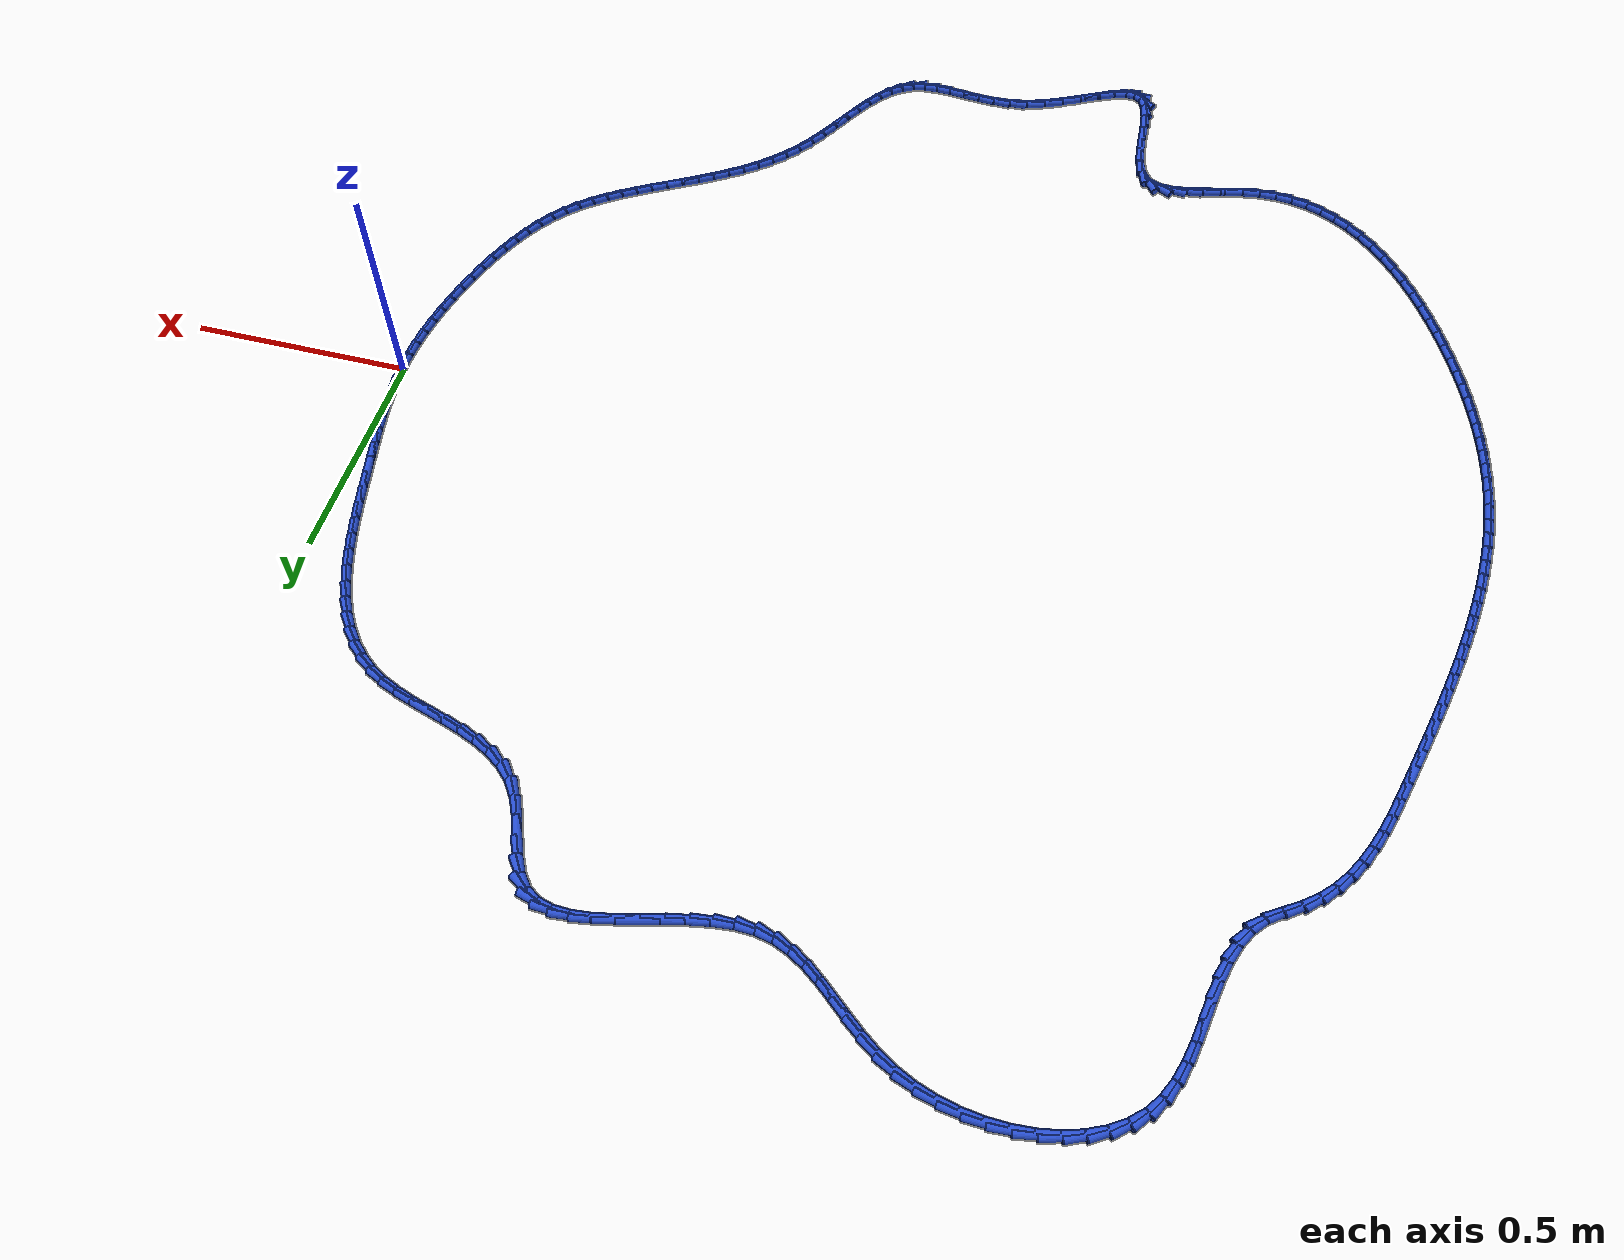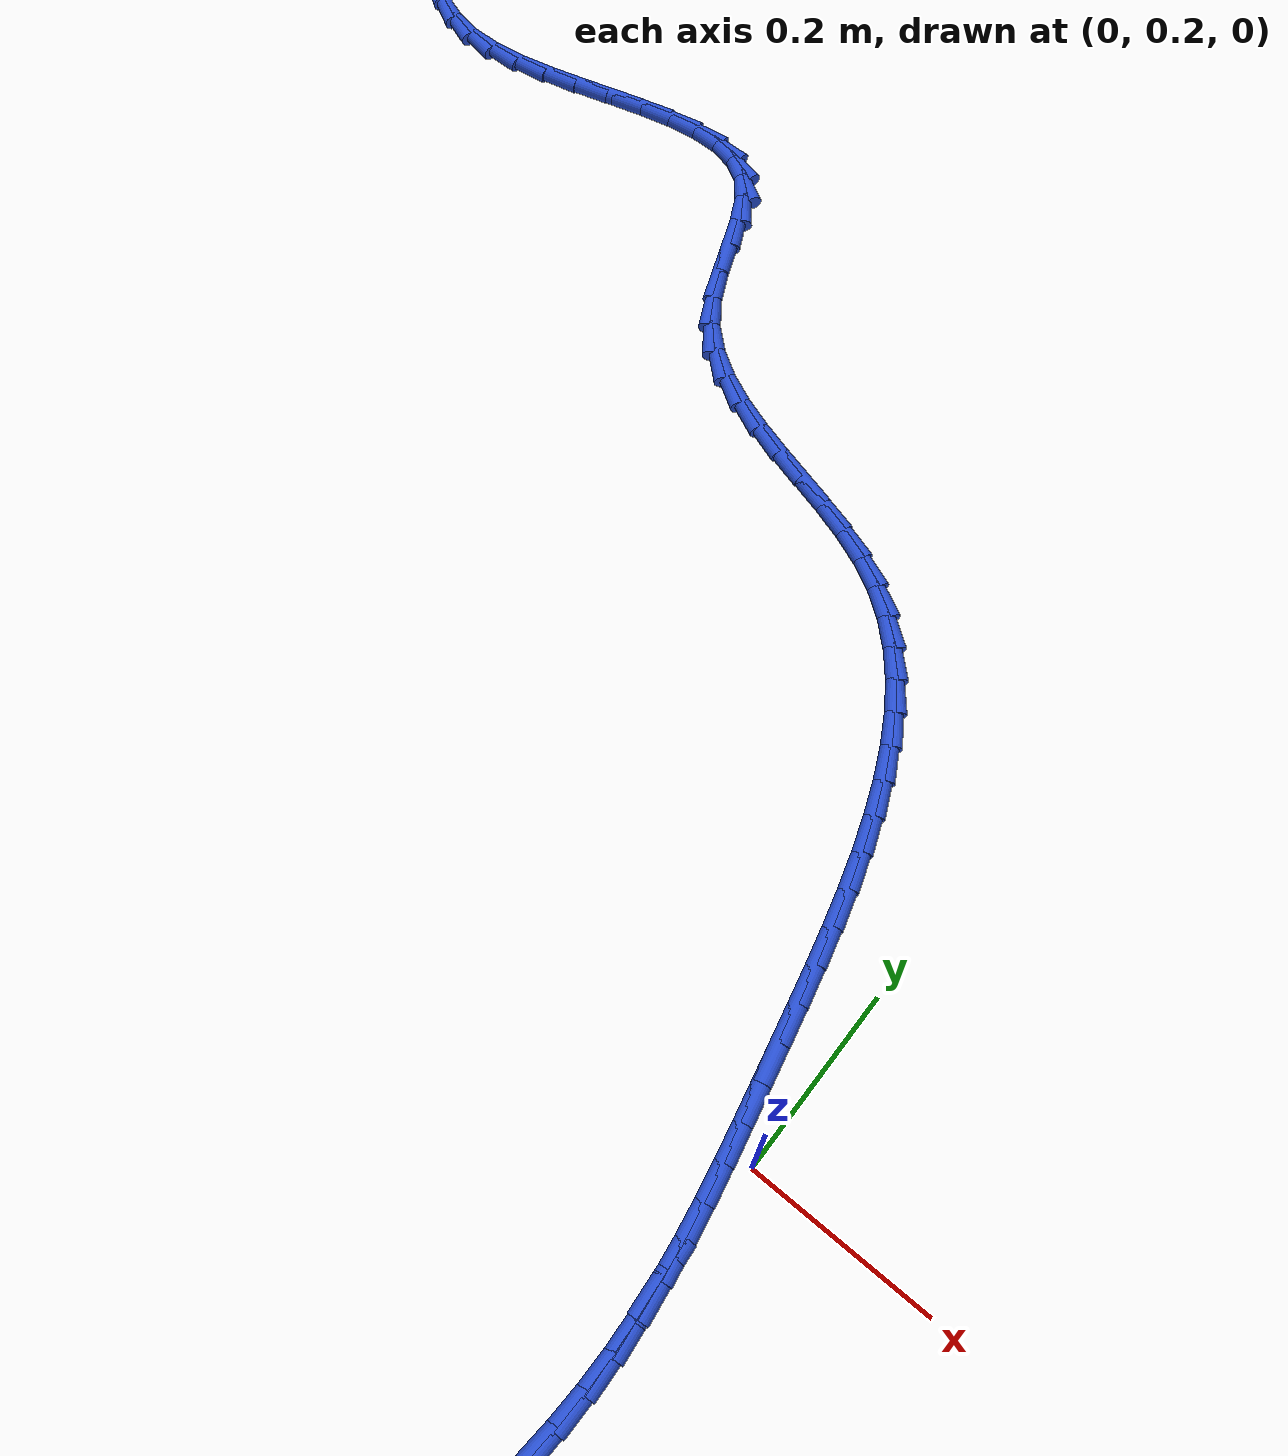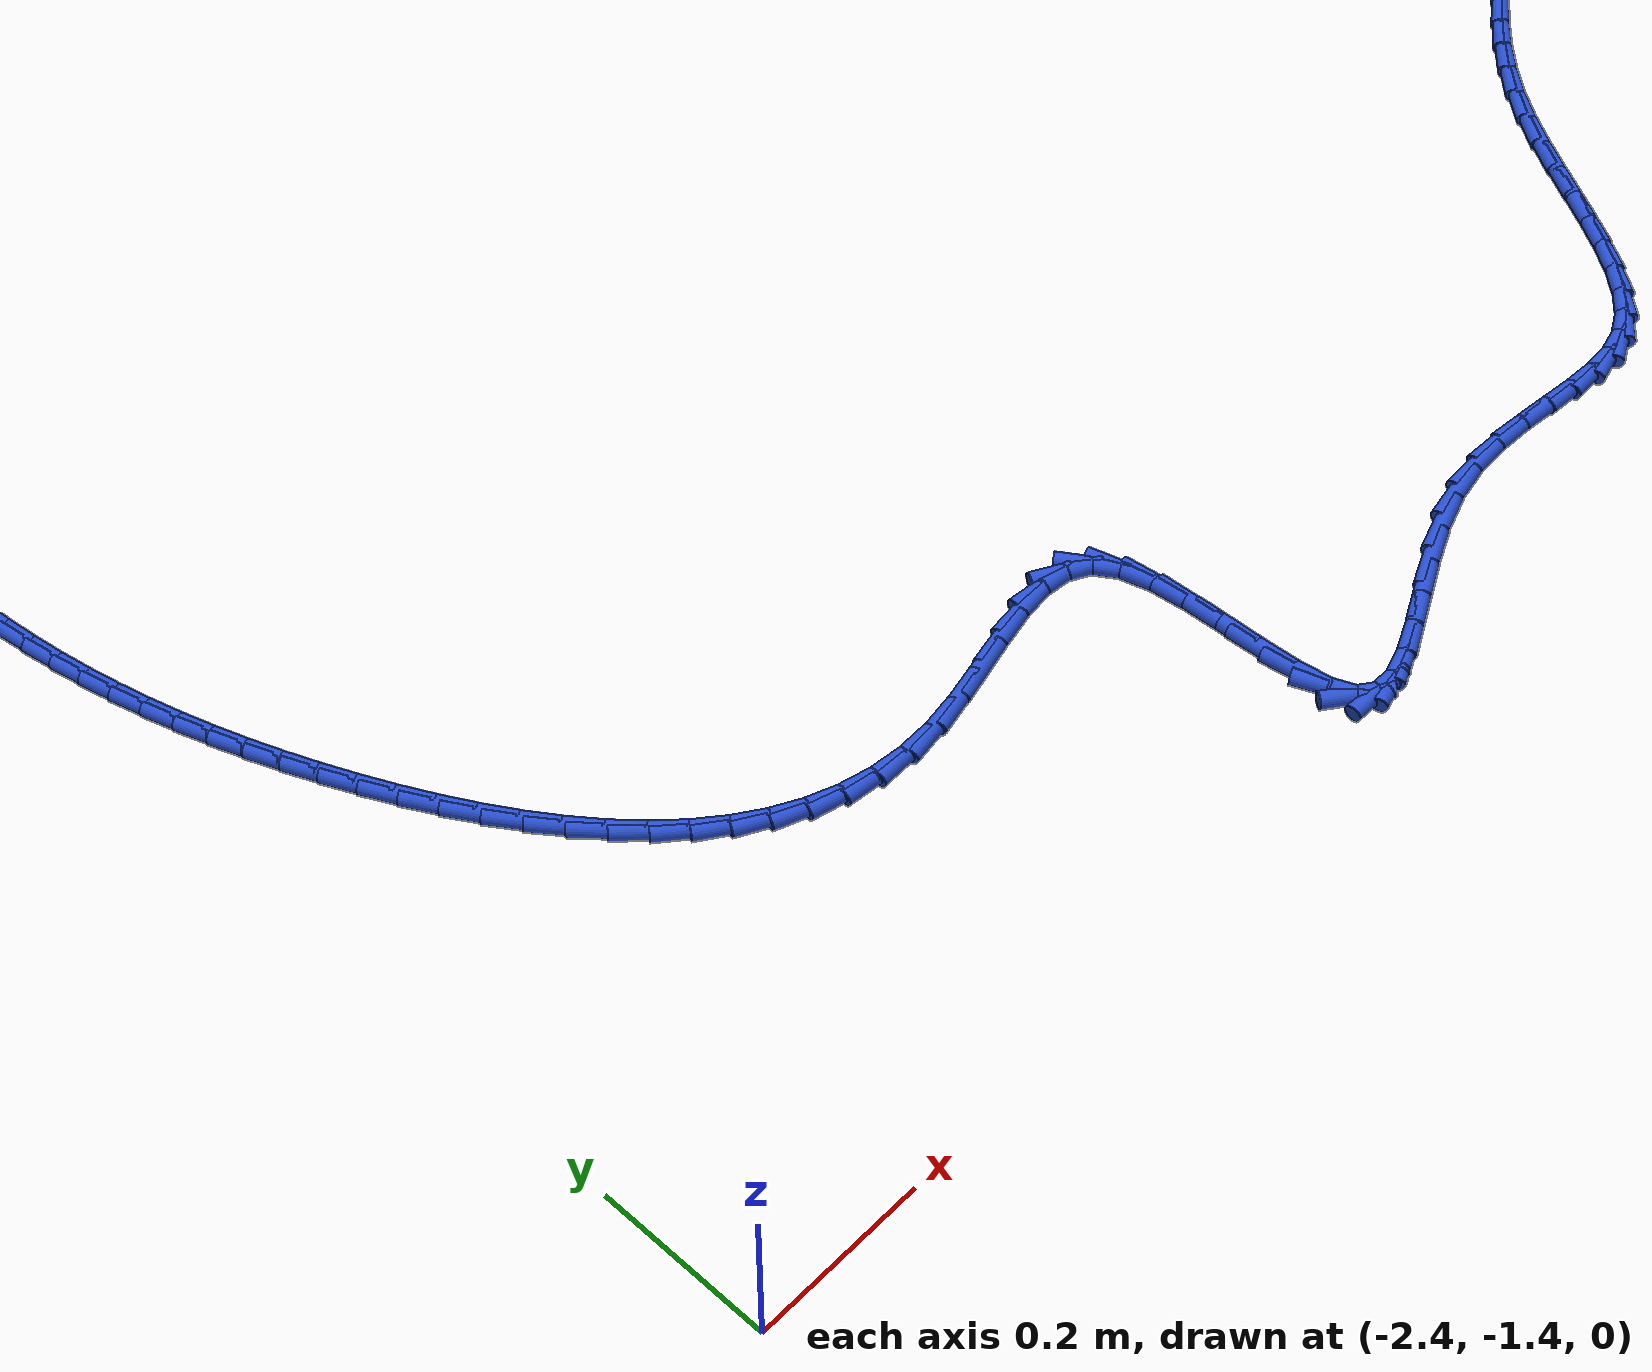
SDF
<sdf version="1.6">
 <world name="default">
  <light name="sun" type="directional">
   <pose>0 0 10 0 -0 0</pose>
   <diffuse>0.8 0.8 0.8 1</diffuse>
   <specular>0.2 0.2 0.2 1</specular>
   <attenuation>
    <range>1000</range>
    <constant>0.9</constant>
    <linear>0.01</linear>
    <quadratic>0.001</quadratic>
   </attenuation>
   <direction>-0.5 0.1 -0.9</direction>
  </light>
  <model name="ground_plane">
   <static>1</static>
   <link name="link">
    <collision name="collision">
     <geometry><plane><normal>0 0 1</normal><size>100 100</size></plane></geometry>
     <surface><friction><ode><mu>100</mu><mu2>50</mu2></ode></friction></surface>
    </collision>
    <visual name="visual">
     <cast_shadows>0</cast_shadows>
     <geometry><plane><normal>0 0 1</normal><size>100 100</size></plane></geometry>
     <material>
      <script><uri>file://media/materials/scripts/gazebo.material</uri><name>Gazebo/WhiteGlow</name></script>
     </material>
    </visual>
   </link>
  </model>
  <gravity>0 0 -9.8</gravity>
  <magnetic_field>6e-06 2.3e-05 -4.2e-05</magnetic_field>
  <atmosphere type="adiabatic"/>
  <physics name="default_physics" default="0" type="ode">
   <max_step_size>0.001</max_step_size>
   <real_time_factor>1</real_time_factor>
   <real_time_update_rate>1000</real_time_update_rate>
  </physics>
  <scene><ambient>0.4 0.4 0.4 1</ambient><background>0.7 0.7 0.7 1</background><shadows>1</shadows></scene>
  <spherical_coordinates>
   <surface_model>EARTH_WGS84</surface_model>
   <latitude_deg>0</latitude_deg>
   <longitude_deg>0</longitude_deg>
   <elevation>0</elevation>
   <heading_deg>0</heading_deg>
  </spherical_coordinates>
  <model name="line">
   <link name="link_0">
    <pose>-1.734723475976807e-18 5.551115123125783e-17 0.01 0 1.57 -1.5294576837806575</pose>
    <collision name="collision">
     <geometry><cylinder><radius>0.01</radius><length>0.08</length></cylinder></geometry>
    </collision>
    <visual name="visual">
     <material>
      <script><name>Gazebo/Blue</name><uri>file://media/materials/scripts/gazebo.material</uri></script>
     </material>
     <geometry><cylinder><radius>0.01</radius><length>0.08</length></cylinder></geometry>
    </visual>
   </link>
   <link name="link_1">
    <pose>-0.0015377222670649787 0.03717698806352743 0.01 0 1.57 -1.484491954047659</pose>
    <collision name="collision">
     <geometry><cylinder><radius>0.01</radius><length>0.08</length></cylinder></geometry>
    </collision>
    <visual name="visual">
     <material>
      <script><name>Gazebo/Blue</name><uri>file://media/materials/scripts/gazebo.material</uri></script>
     </material>
     <geometry><cylinder><radius>0.01</radius><length>0.08</length></cylinder></geometry>
    </visual>
   </link>
   <link name="link_2">
    <pose>-0.004746334633091138 0.07426250198212336 0.01 0 1.57 -1.4463033006279675</pose>
    <collision name="collision">
     <geometry><cylinder><radius>0.01</radius><length>0.08</length></cylinder></geometry>
    </collision>
    <visual name="visual">
     <material>
      <script><name>Gazebo/Blue</name><uri>file://media/materials/scripts/gazebo.material</uri></script>
     </material>
     <geometry><cylinder><radius>0.01</radius><length>0.08</length></cylinder></geometry>
    </visual>
   </link>
   <link name="link_3">
    <pose>-0.009392195554723455 0.1113877524114802 0.01 0 1.57 -1.4152254693113606</pose>
    <collision name="collision">
     <geometry><cylinder><radius>0.01</radius><length>0.08</length></cylinder></geometry>
    </collision>
    <visual name="visual">
     <material>
      <script><name>Gazebo/Blue</name><uri>file://media/materials/scripts/gazebo.material</uri></script>
     </material>
     <geometry><cylinder><radius>0.01</radius><length>0.08</length></cylinder></geometry>
    </visual>
   </link>
   <link name="link_4">
    <pose>-0.015241663488606907 0.1486839500072904 0.01 0 1.57 -1.3913710444587293</pose>
    <collision name="collision">
     <geometry><cylinder><radius>0.01</radius><length>0.08</length></cylinder></geometry>
    </collision>
    <visual name="visual">
     <material>
      <script><name>Gazebo/Blue</name><uri>file://media/materials/scripts/gazebo.material</uri></script>
     </material>
     <geometry><cylinder><radius>0.01</radius><length>0.08</length></cylinder></geometry>
    </visual>
   </link>
   <link name="link_5">
    <pose>-0.022061096891386463 0.1862823054252463 0.01 0 1.57 -1.3746800725791712</pose>
    <collision name="collision">
     <geometry><cylinder><radius>0.01</radius><length>0.08</length></cylinder></geometry>
    </collision>
    <visual name="visual">
     <material>
      <script><name>Gazebo/Blue</name><uri>file://media/materials/scripts/gazebo.material</uri></script>
     </material>
     <geometry><cylinder><radius>0.01</radius><length>0.08</length></cylinder></geometry>
    </visual>
   </link>
   <link name="link_6">
    <pose>-0.029616854219707115 0.2243140293210403 0.01 0 1.57 -1.364965352702498</pose>
    <collision name="collision">
     <geometry><cylinder><radius>0.01</radius><length>0.08</length></cylinder></geometry>
    </collision>
    <visual name="visual">
     <material>
      <script><name>Gazebo/Blue</name><uri>file://media/materials/scripts/gazebo.material</uri></script>
     </material>
     <geometry><cylinder><radius>0.01</radius><length>0.08</length></cylinder></geometry>
    </visual>
   </link>
   <link name="link_7">
    <pose>-0.03767529393021382 0.26291033235036476 0.01 0 1.57 -1.3619333168266203</pose>
    <collision name="collision">
     <geometry><cylinder><radius>0.01</radius><length>0.08</length></cylinder></geometry>
    </collision>
    <visual name="visual">
     <material>
      <script><name>Gazebo/Blue</name><uri>file://media/materials/scripts/gazebo.material</uri></script>
     </material>
     <geometry><cylinder><radius>0.01</radius><length>0.08</length></cylinder></geometry>
    </visual>
   </link>
   <link name="link_8">
    <pose>-0.04600330266257185 0.3022019014968688 0.01 0 1.57 -1.3614533639277937</pose>
    <collision name="collision">
     <geometry><cylinder><radius>0.01</radius><length>0.08</length></cylinder></geometry>
    </collision>
    <visual name="visual">
     <material>
      <script><name>Gazebo/Blue</name><uri>file://media/materials/scripts/gazebo.material</uri></script>
     </material>
     <geometry><cylinder><radius>0.01</radius><length>0.08</length></cylinder></geometry>
    </visual>
   </link>
   <link name="link_9">
    <pose>-0.05449887943713009 0.3421894311362031 0.01 0 1.57 -1.3547385110409924</pose>
    <collision name="collision">
     <geometry><cylinder><radius>0.01</radius><length>0.08</length></cylinder></geometry>
    </collision>
    <visual name="visual">
     <material>
      <script><name>Gazebo/Blue</name><uri>file://media/materials/scripts/gazebo.material</uri></script>
     </material>
     <geometry><cylinder><radius>0.01</radius><length>0.08</length></cylinder></geometry>
    </visual>
   </link>
   <link name="link_10">
    <pose>-0.0633625610124835 0.3825736617463969 0.01 0 1.57 -1.3406506359792119</pose>
    <collision name="collision">
     <geometry><cylinder><radius>0.01</radius><length>0.08</length></cylinder></geometry>
    </collision>
    <visual name="visual">
     <material>
      <script><name>Gazebo/Blue</name><uri>file://media/materials/scripts/gazebo.material</uri></script>
     </material>
     <geometry><cylinder><radius>0.01</radius><length>0.08</length></cylinder></geometry>
    </visual>
   </link>
   <link name="link_11">
    <pose>-0.07283741697235752 0.42301316423434215 0.01 0 1.57 -1.3190139921230886</pose>
    <collision name="collision">
     <geometry><cylinder><radius>0.01</radius><length>0.08</length></cylinder></geometry>
    </collision>
    <visual name="visual">
     <material>
      <script><name>Gazebo/Blue</name><uri>file://media/materials/scripts/gazebo.material</uri></script>
     </material>
     <geometry><cylinder><radius>0.01</radius><length>0.08</length></cylinder></geometry>
    </visual>
   </link>
   <link name="link_12">
    <pose>-0.08316651690047758 0.4631665095069303 0.01 0 1.57 -1.2893805738168183</pose>
    <collision name="collision">
     <geometry><cylinder><radius>0.01</radius><length>0.08</length></cylinder></geometry>
    </collision>
    <visual name="visual">
     <material>
      <script><name>Gazebo/Blue</name><uri>file://media/materials/scripts/gazebo.material</uri></script>
     </material>
     <geometry><cylinder><radius>0.01</radius><length>0.08</length></cylinder></geometry>
    </visual>
   </link>
   <link name="link_13">
    <pose>-0.09459293038056912 0.5026922684710534 0.01 0 1.57 -1.2510417184283502</pose>
    <collision name="collision">
     <geometry><cylinder><radius>0.01</radius><length>0.08</length></cylinder></geometry>
    </collision>
    <visual name="visual">
     <material>
      <script><name>Gazebo/Blue</name><uri>file://media/materials/scripts/gazebo.material</uri></script>
     </material>
     <geometry><cylinder><radius>0.01</radius><length>0.08</length></cylinder></geometry>
    </visual>
   </link>
   <link name="link_14">
    <pose>-0.10735972699635767 0.5412490120336034 0.01 0 1.57 -1.2030437643708274</pose>
    <collision name="collision">
     <geometry><cylinder><radius>0.01</radius><length>0.08</length></cylinder></geometry>
    </collision>
    <visual name="visual">
     <material>
      <script><name>Gazebo/Blue</name><uri>file://media/materials/scripts/gazebo.material</uri></script>
     </material>
     <geometry><cylinder><radius>0.01</radius><length>0.08</length></cylinder></geometry>
    </visual>
   </link>
   <link name="link_15">
    <pose>-0.12170997633156855 0.5784953111014715 0.01 0 1.57 -1.1442273392983884</pose>
    <collision name="collision">
     <geometry><cylinder><radius>0.01</radius><length>0.08</length></cylinder></geometry>
    </collision>
    <visual name="visual">
     <material>
      <script><name>Gazebo/Blue</name><uri>file://media/materials/scripts/gazebo.material</uri></script>
     </material>
     <geometry><cylinder><radius>0.01</radius><length>0.08</length></cylinder></geometry>
    </visual>
   </link>
   <link name="link_16">
    <pose>-0.13788674796992728 0.6140897365815496 0.01 0 1.57 -1.0733213535850863</pose>
    <collision name="collision">
     <geometry><cylinder><radius>0.01</radius><length>0.08</length></cylinder></geometry>
    </collision>
    <visual name="visual">
     <material>
      <script><name>Gazebo/Blue</name><uri>file://media/materials/scripts/gazebo.material</uri></script>
     </material>
     <geometry><cylinder><radius>0.01</radius><length>0.08</length></cylinder></geometry>
    </visual>
   </link>
   <link name="link_17">
    <pose>-0.1561331114951593 0.6476908593807302 0.01 0 1.57 -0.989136097998022</pose>
    <collision name="collision">
     <geometry><cylinder><radius>0.01</radius><length>0.08</length></cylinder></geometry>
    </collision>
    <visual name="visual">
     <material>
      <script><name>Gazebo/Blue</name><uri>file://media/materials/scripts/gazebo.material</uri></script>
     </material>
     <geometry><cylinder><radius>0.01</radius><length>0.08</length></cylinder></geometry>
    </visual>
   </link>
   <link name="link_18">
    <pose>-0.17669213649099003 0.6789572504059043 0.01 0 1.57 -0.8909033180250826</pose>
    <collision name="collision">
     <geometry><cylinder><radius>0.01</radius><length>0.08</length></cylinder></geometry>
    </collision>
    <visual name="visual">
     <material>
      <script><name>Gazebo/Blue</name><uri>file://media/materials/scripts/gazebo.material</uri></script>
     </material>
     <geometry><cylinder><radius>0.01</radius><length>0.08</length></cylinder></geometry>
    </visual>
   </link>
   <link name="link_19">
    <pose>-0.19980689254114503 0.707547480563964 0.01 0 1.57 -0.7787767477814497</pose>
    <collision name="collision">
     <geometry><cylinder><radius>0.01</radius><length>0.08</length></cylinder></geometry>
    </collision>
    <visual name="visual">
     <material>
      <script><name>Gazebo/Blue</name><uri>file://media/materials/scripts/gazebo.material</uri></script>
     </material>
     <geometry><cylinder><radius>0.01</radius><length>0.08</length></cylinder></geometry>
    </visual>
   </link>
   <link name="link_20">
    <pose>-0.22572044922934956 0.7331201207618007 0.01 0 1.57 -0.6543971799876047</pose>
    <collision name="collision">
     <geometry><cylinder><radius>0.01</radius><length>0.08</length></cylinder></geometry>
    </collision>
    <visual name="visual">
     <material>
      <script><name>Gazebo/Blue</name><uri>file://media/materials/scripts/gazebo.material</uri></script>
     </material>
     <geometry><cylinder><radius>0.01</radius><length>0.08</length></cylinder></geometry>
    </visual>
   </link>
   <link name="link_21">
    <pose>-0.25467587613932924 0.7553337419063069 0.01 0 1.57 -0.5226803373683583</pose>
    <collision name="collision">
     <geometry><cylinder><radius>0.01</radius><length>0.08</length></cylinder></geometry>
    </collision>
    <visual name="visual">
     <material>
      <script><name>Gazebo/Blue</name><uri>file://media/materials/scripts/gazebo.material</uri></script>
     </material>
     <geometry><cylinder><radius>0.01</radius><length>0.08</length></cylinder></geometry>
    </visual>
   </link>
   <link name="link_22">
    <pose>-0.28688205316683263 0.7738885685946216 0.01 0 1.57 -0.41117091191270355</pose>
    <collision name="collision">
     <geometry><cylinder><radius>0.01</radius><length>0.08</length></cylinder></geometry>
    </collision>
    <visual name="visual">
     <material>
      <script><name>Gazebo/Blue</name><uri>file://media/materials/scripts/gazebo.material</uri></script>
     </material>
     <geometry><cylinder><radius>0.01</radius><length>0.08</length></cylinder></geometry>
    </visual>
   </link>
   <link name="link_23">
    <pose>-0.32197065468517044 0.789188041553179 0.01 0 1.57 -0.33763852767384994</pose>
    <collision name="collision">
     <geometry><cylinder><radius>0.01</radius><length>0.08</length></cylinder></geometry>
    </collision>
    <visual name="visual">
     <material>
      <script><name>Gazebo/Blue</name><uri>file://media/materials/scripts/gazebo.material</uri></script>
     </material>
     <geometry><cylinder><radius>0.01</radius><length>0.08</length></cylinder></geometry>
    </visual>
   </link>
   <link name="link_24">
    <pose>-0.3590928662386772 0.8022209865772467 0.01 0 1.57 -0.2982798082437698</pose>
    <collision name="collision">
     <geometry><cylinder><radius>0.01</radius><length>0.08</length></cylinder></geometry>
    </collision>
    <visual name="visual">
     <material>
      <script><name>Gazebo/Blue</name><uri>file://media/materials/scripts/gazebo.material</uri></script>
     </material>
     <geometry><cylinder><radius>0.01</radius><length>0.08</length></cylinder></geometry>
    </visual>
   </link>
   <link name="link_25">
    <pose>-0.39738523119453767 0.8139940681949837 0.01 0 1.57 -0.2900339981419908</pose>
    <collision name="collision">
     <geometry><cylinder><radius>0.01</radius><length>0.08</length></cylinder></geometry>
    </collision>
    <visual name="visual">
     <material>
      <script><name>Gazebo/Blue</name><uri>file://media/materials/scripts/gazebo.material</uri></script>
     </material>
     <geometry><cylinder><radius>0.01</radius><length>0.08</length></cylinder></geometry>
    </visual>
   </link>
   <link name="link_26">
    <pose>-0.43598429291993723 0.8255139509345507 0.01 0 1.57 -0.31208112287291845</pose>
    <collision name="collision">
     <geometry><cylinder><radius>0.01</radius><length>0.08</length></cylinder></geometry>
    </collision>
    <visual name="visual">
     <material>
      <script><name>Gazebo/Blue</name><uri>file://media/materials/scripts/gazebo.material</uri></script>
     </material>
     <geometry><cylinder><radius>0.01</radius><length>0.08</length></cylinder></geometry>
    </visual>
   </link>
   <link name="link_27">
    <pose>-0.4740265947820609 0.8377872993241077 0.01 0 1.57 -0.36593777058597304</pose>
    <collision name="collision">
     <geometry><cylinder><radius>0.01</radius><length>0.08</length></cylinder></geometry>
    </collision>
    <visual name="visual">
     <material>
      <script><name>Gazebo/Blue</name><uri>file://media/materials/scripts/gazebo.material</uri></script>
     </material>
     <geometry><cylinder><radius>0.01</radius><length>0.08</length></cylinder></geometry>
    </visual>
   </link>
   <link name="link_28">
    <pose>-0.5106486801480934 0.851820777891814 0.01 0 1.57 -0.455015503073997</pose>
    <collision name="collision">
     <geometry><cylinder><radius>0.01</radius><length>0.08</length></cylinder></geometry>
    </collision>
    <visual name="visual">
     <material>
      <script><name>Gazebo/Blue</name><uri>file://media/materials/scripts/gazebo.material</uri></script>
     </material>
     <geometry><cylinder><radius>0.01</radius><length>0.08</length></cylinder></geometry>
    </visual>
   </link>
   <link name="link_29">
    <pose>-0.5449870923852201 0.8686210511658301 0.01 0 1.57 -0.5830934907984354</pose>
    <collision name="collision">
     <geometry><cylinder><radius>0.01</radius><length>0.08</length></cylinder></geometry>
    </collision>
    <visual name="visual">
     <material>
      <script><name>Gazebo/Blue</name><uri>file://media/materials/scripts/gazebo.material</uri></script>
     </material>
     <geometry><cylinder><radius>0.01</radius><length>0.08</length></cylinder></geometry>
    </visual>
   </link>
   <link name="link_30">
    <pose>-0.5761783748606262 0.8891947836743164 0.01 0 1.57 -0.750638107358285</pose>
    <collision name="collision">
     <geometry><cylinder><radius>0.01</radius><length>0.08</length></cylinder></geometry>
    </collision>
    <visual name="visual">
     <material>
      <script><name>Gazebo/Blue</name><uri>file://media/materials/scripts/gazebo.material</uri></script>
     </material>
     <geometry><cylinder><radius>0.01</radius><length>0.08</length></cylinder></geometry>
    </visual>
   </link>
   <link name="link_31">
    <pose>-0.6033590709414962 0.9145486399454319 0.01 0 1.57 -0.9474467181236057</pose>
    <collision name="collision">
     <geometry><cylinder><radius>0.01</radius><length>0.08</length></cylinder></geometry>
    </collision>
    <visual name="visual">
     <material>
      <script><name>Gazebo/Blue</name><uri>file://media/materials/scripts/gazebo.material</uri></script>
     </material>
     <geometry><cylinder><radius>0.01</radius><length>0.08</length></cylinder></geometry>
    </visual>
   </link>
   <link name="link_32">
    <pose>-0.6257071221112285 0.9456317233077048 0.01 0 1.57 -1.1073831744566363</pose>
    <collision name="collision">
     <geometry><cylinder><radius>0.01</radius><length>0.08</length></cylinder></geometry>
    </collision>
    <visual name="visual">
     <material>
      <script><name>Gazebo/Blue</name><uri>file://media/materials/scripts/gazebo.material</uri></script>
     </material>
     <geometry><cylinder><radius>0.01</radius><length>0.08</length></cylinder></geometry>
    </visual>
   </link>
   <link name="link_33">
    <pose>-0.6436845645640886 0.9816076927564277 0.01 0 1.57 -1.1814205723311484</pose>
    <collision name="collision">
     <geometry><cylinder><radius>0.01</radius><length>0.08</length></cylinder></geometry>
    </collision>
    <visual name="visual">
     <material>
      <script><name>Gazebo/Blue</name><uri>file://media/materials/scripts/gazebo.material</uri></script>
     </material>
     <geometry><cylinder><radius>0.01</radius><length>0.08</length></cylinder></geometry>
    </visual>
   </link>
   <link name="link_34">
    <pose>-0.6592545127883546 1.0195530623815323 0.01 0 1.57 -1.179546488560856</pose>
    <collision name="collision">
     <geometry><cylinder><radius>0.01</radius><length>0.08</length></cylinder></geometry>
    </collision>
    <visual name="visual">
     <material>
      <script><name>Gazebo/Blue</name><uri>file://media/materials/scripts/gazebo.material</uri></script>
     </material>
     <geometry><cylinder><radius>0.01</radius><length>0.08</length></cylinder></geometry>
    </visual>
   </link>
   <link name="link_35">
    <pose>-0.6744652079903459 1.056425983495619 0.01 0 1.57 -1.0945216091758796</pose>
    <collision name="collision">
     <geometry><cylinder><radius>0.01</radius><length>0.08</length></cylinder></geometry>
    </collision>
    <visual name="visual">
     <material>
      <script><name>Gazebo/Blue</name><uri>file://media/materials/scripts/gazebo.material</uri></script>
     </material>
     <geometry><cylinder><radius>0.01</radius><length>0.08</length></cylinder></geometry>
    </visual>
   </link>
   <link name="link_36">
    <pose>-0.6913648913763834 1.0891846074112874 0.01 0 1.57 -0.892387288345922</pose>
    <collision name="collision">
     <geometry><cylinder><radius>0.01</radius><length>0.08</length></cylinder></geometry>
    </collision>
    <visual name="visual">
     <material>
      <script><name>Gazebo/Blue</name><uri>file://media/materials/scripts/gazebo.material</uri></script>
     </material>
     <geometry><cylinder><radius>0.01</radius><length>0.08</length></cylinder></geometry>
    </visual>
   </link>
   <link name="link_37">
    <pose>-0.7120016040296608 1.1147874079938682 0.01 0 1.57 -0.5641040190735358</pose>
    <collision name="collision">
     <geometry><cylinder><radius>0.01</radius><length>0.08</length></cylinder></geometry>
    </collision>
    <visual name="visual">
     <material>
      <script><name>Gazebo/Blue</name><uri>file://media/materials/scripts/gazebo.material</uri></script>
     </material>
     <geometry><cylinder><radius>0.01</radius><length>0.08</length></cylinder></geometry>
    </visual>
   </link>
   <link name="link_38">
    <pose>-0.7378392260667642 1.131134393044629 0.01 0 1.57 -0.2554464483704133</pose>
    <collision name="collision">
     <geometry><cylinder><radius>0.01</radius><length>0.08</length></cylinder></geometry>
    </collision>
    <visual name="visual">
     <material>
      <script><name>Gazebo/Blue</name><uri>file://media/materials/scripts/gazebo.material</uri></script>
     </material>
     <geometry><cylinder><radius>0.01</radius><length>0.08</length></cylinder></geometry>
    </visual>
   </link>
   <link name="link_39">
    <pose>-0.768474566804585 1.1391348616718489 0.01 0 1.57 -0.033549782701388635</pose>
    <collision name="collision">
     <geometry><cylinder><radius>0.01</radius><length>0.08</length></cylinder></geometry>
    </collision>
    <visual name="visual">
     <material>
      <script><name>Gazebo/Blue</name><uri>file://media/materials/scripts/gazebo.material</uri></script>
     </material>
     <geometry><cylinder><radius>0.01</radius><length>0.08</length></cylinder></geometry>
    </visual>
   </link>
   <link name="link_40">
    <pose>-0.8031322105870096 1.1402980545477268 0.01 0 1.57 0.10943815288981638</pose>
    <collision name="collision">
     <geometry><cylinder><radius>0.01</radius><length>0.08</length></cylinder></geometry>
    </collision>
    <visual name="visual">
     <material>
      <script><name>Gazebo/Blue</name><uri>file://media/materials/scripts/gazebo.material</uri></script>
     </material>
     <geometry><cylinder><radius>0.01</radius><length>0.08</length></cylinder></geometry>
    </visual>
   </link>
   <link name="link_41">
    <pose>-0.8410367417579238 1.1361332123444616 0.01 0 1.57 0.19521405236376452</pose>
    <collision name="collision">
     <geometry><cylinder><radius>0.01</radius><length>0.08</length></cylinder></geometry>
    </collision>
    <visual name="visual">
     <material>
      <script><name>Gazebo/Blue</name><uri>file://media/materials/scripts/gazebo.material</uri></script>
     </material>
     <geometry><cylinder><radius>0.01</radius><length>0.08</length></cylinder></geometry>
    </visual>
   </link>
   <link name="link_42">
    <pose>-0.8814127446612147 1.128149575734253 0.01 0 1.57 0.23994292107422835</pose>
    <collision name="collision">
     <geometry><cylinder><radius>0.01</radius><length>0.08</length></cylinder></geometry>
    </collision>
    <visual name="visual">
     <material>
      <script><name>Gazebo/Blue</name><uri>file://media/materials/scripts/gazebo.material</uri></script>
     </material>
     <geometry><cylinder><radius>0.01</radius><length>0.08</length></cylinder></geometry>
    </visual>
   </link>
   <link name="link_43">
    <pose>-0.9234848036407683 1.117856385389299 0.01 0 1.57 0.25252403384447536</pose>
    <collision name="collision">
     <geometry><cylinder><radius>0.01</radius><length>0.08</length></cylinder></geometry>
    </collision>
    <visual name="visual">
     <material>
      <script><name>Gazebo/Blue</name><uri>file://media/materials/scripts/gazebo.material</uri></script>
     </material>
     <geometry><cylinder><radius>0.01</radius><length>0.08</length></cylinder></geometry>
    </visual>
   </link>
   <link name="link_44">
    <pose>-0.9664775030404708 1.106762881981799 0.01 0 1.57 0.23623474272362704</pose>
    <collision name="collision">
     <geometry><cylinder><radius>0.01</radius><length>0.08</length></cylinder></geometry>
    </collision>
    <visual name="visual">
     <material>
      <script><name>Gazebo/Blue</name><uri>file://media/materials/scripts/gazebo.material</uri></script>
     </material>
     <geometry><cylinder><radius>0.01</radius><length>0.08</length></cylinder></geometry>
    </visual>
   </link>
   <link name="link_45">
    <pose>-1.0096154272042088 1.096378306183952 0.01 0 1.57 0.1898032400876308</pose>
    <collision name="collision">
     <geometry><cylinder><radius>0.01</radius><length>0.08</length></cylinder></geometry>
    </collision>
    <visual name="visual">
     <material>
      <script><name>Gazebo/Blue</name><uri>file://media/materials/scripts/gazebo.material</uri></script>
     </material>
     <geometry><cylinder><radius>0.01</radius><length>0.08</length></cylinder></geometry>
    </visual>
   </link>
   <link name="link_46">
    <pose>-1.0521231604758687 1.0882118986679565 0.01 0 1.57 0.10758226188313813</pose>
    <collision name="collision">
     <geometry><cylinder><radius>0.01</radius><length>0.08</length></cylinder></geometry>
    </collision>
    <visual name="visual">
     <material>
      <script><name>Gazebo/Blue</name><uri>file://media/materials/scripts/gazebo.material</uri></script>
     </material>
     <geometry><cylinder><radius>0.01</radius><length>0.08</length></cylinder></geometry>
    </visual>
   </link>
   <link name="link_47">
    <pose>-1.0932252871993366 1.0837729001060121 0.01 0 1.57 -0.0204911815716287</pose>
    <collision name="collision">
     <geometry><cylinder><radius>0.01</radius><length>0.08</length></cylinder></geometry>
    </collision>
    <visual name="visual">
     <material>
      <script><name>Gazebo/Blue</name><uri>file://media/materials/scripts/gazebo.material</uri></script>
     </material>
     <geometry><cylinder><radius>0.01</radius><length>0.08</length></cylinder></geometry>
    </visual>
   </link>
   <link name="link_48">
    <pose>-1.132146391718499 1.0845705511703168 0.01 0 1.57 -0.19960332465317576</pose>
    <collision name="collision">
     <geometry><cylinder><radius>0.01</radius><length>0.08</length></cylinder></geometry>
    </collision>
    <visual name="visual">
     <material>
      <script><name>Gazebo/Blue</name><uri>file://media/materials/scripts/gazebo.material</uri></script>
     </material>
     <geometry><cylinder><radius>0.01</radius><length>0.08</length></cylinder></geometry>
    </visual>
   </link>
   <link name="link_49">
    <pose>-1.1682404359963554 1.0918722714173559 0.01 0 1.57 -0.37834428846003815</pose>
    <collision name="collision">
     <geometry><cylinder><radius>0.01</radius><length>0.08</length></cylinder></geometry>
    </collision>
    <visual name="visual">
     <material>
      <script><name>Gazebo/Blue</name><uri>file://media/materials/scripts/gazebo.material</uri></script>
     </material>
     <geometry><cylinder><radius>0.01</radius><length>0.08</length></cylinder></geometry>
    </visual>
   </link>
   <link name="link_50">
    <pose>-1.2017907781969286 1.1052083358509976 0.01 0 1.57 -0.5198376043215917</pose>
    <collision name="collision">
     <geometry><cylinder><radius>0.01</radius><length>0.08</length></cylinder></geometry>
    </collision>
    <visual name="visual">
     <material>
      <script><name>Gazebo/Blue</name><uri>file://media/materials/scripts/gazebo.material</uri></script>
     </material>
     <geometry><cylinder><radius>0.01</radius><length>0.08</length></cylinder></geometry>
    </visual>
   </link>
   <link name="link_51">
    <pose>-1.2334870795388595 1.1233495940145137 0.01 0 1.57 -0.6181726960812451</pose>
    <collision name="collision">
     <geometry><cylinder><radius>0.01</radius><length>0.08</length></cylinder></geometry>
    </collision>
    <visual name="visual">
     <material>
      <script><name>Gazebo/Blue</name><uri>file://media/materials/scripts/gazebo.material</uri></script>
     </material>
     <geometry><cylinder><radius>0.01</radius><length>0.08</length></cylinder></geometry>
    </visual>
   </link>
   <link name="link_52">
    <pose>-1.2640207079785504 1.1450637053690556 0.01 0 1.57 -0.6748375878534358</pose>
    <collision name="collision">
     <geometry><cylinder><radius>0.01</radius><length>0.08</length></cylinder></geometry>
    </collision>
    <visual name="visual">
     <material>
      <script><name>Gazebo/Blue</name><uri>file://media/materials/scripts/gazebo.material</uri></script>
     </material>
     <geometry><cylinder><radius>0.01</radius><length>0.08</length></cylinder></geometry>
    </visual>
   </link>
   <link name="link_53">
    <pose>-1.2940830314724023 1.1691183293757728 0.01 0 1.57 -0.6933231745169215</pose>
    <collision name="collision">
     <geometry><cylinder><radius>0.01</radius><length>0.08</length></cylinder></geometry>
    </collision>
    <visual name="visual">
     <material>
      <script><name>Gazebo/Blue</name><uri>file://media/materials/scripts/gazebo.material</uri></script>
     </material>
     <geometry><cylinder><radius>0.01</radius><length>0.08</length></cylinder></geometry>
    </visual>
   </link>
   <link name="link_54">
    <pose>-1.3243654179768183 1.1942811254958166 0.01 0 1.57 -0.676372452242011</pose>
    <collision name="collision">
     <geometry><cylinder><radius>0.01</radius><length>0.08</length></cylinder></geometry>
    </collision>
    <visual name="visual">
     <material>
      <script><name>Gazebo/Blue</name><uri>file://media/materials/scripts/gazebo.material</uri></script>
     </material>
     <geometry><cylinder><radius>0.01</radius><length>0.08</length></cylinder></geometry>
    </visual>
   </link>
   <link name="link_55">
    <pose>-1.3555592354481987 1.219319753190338 0.01 0 1.57 -0.625398338599004</pose>
    <collision name="collision">
     <geometry><cylinder><radius>0.01</radius><length>0.08</length></cylinder></geometry>
    </collision>
    <visual name="visual">
     <material>
      <script><name>Gazebo/Blue</name><uri>file://media/materials/scripts/gazebo.material</uri></script>
     </material>
     <geometry><cylinder><radius>0.01</radius><length>0.08</length></cylinder></geometry>
    </visual>
   </link>
   <link name="link_56">
    <pose>-1.3883558518429455 1.2430018719204872 0.01 0 1.57 -0.5412321054823621</pose>
    <collision name="collision">
     <geometry><cylinder><radius>0.01</radius><length>0.08</length></cylinder></geometry>
    </collision>
    <visual name="visual">
     <material>
      <script><name>Gazebo/Blue</name><uri>file://media/materials/scripts/gazebo.material</uri></script>
     </material>
     <geometry><cylinder><radius>0.01</radius><length>0.08</length></cylinder></geometry>
    </visual>
   </link>
   <link name="link_57">
    <pose>-1.4234466351174613 1.2640951411474153 0.01 0 1.57 -0.43001432449342347</pose>
    <collision name="collision">
     <geometry><cylinder><radius>0.01</radius><length>0.08</length></cylinder></geometry>
    </collision>
    <visual name="visual">
     <material>
      <script><name>Gazebo/Blue</name><uri>file://media/materials/scripts/gazebo.material</uri></script>
     </material>
     <geometry><cylinder><radius>0.01</radius><length>0.08</length></cylinder></geometry>
    </visual>
   </link>
   <link name="link_58">
    <pose>-1.4613728881119246 1.281489575660048 0.01 0 1.57 -0.319586727207389</pose>
    <collision name="collision">
     <geometry><cylinder><radius>0.01</radius><length>0.08</length></cylinder></geometry>
    </collision>
    <visual name="visual">
     <material>
      <script><name>Gazebo/Blue</name><uri>file://media/materials/scripts/gazebo.material</uri></script>
     </material>
     <geometry><cylinder><radius>0.01</radius><length>0.08</length></cylinder></geometry>
    </visual>
   </link>
   <link name="link_59">
    <pose>-1.501731266618996 1.2948454065510082 0.01 0 1.57 -0.2172741119044394</pose>
    <collision name="collision">
     <geometry><cylinder><radius>0.01</radius><length>0.08</length></cylinder></geometry>
    </collision>
    <visual name="visual">
     <material>
      <script><name>Gazebo/Blue</name><uri>file://media/materials/scripts/gazebo.material</uri></script>
     </material>
     <geometry><cylinder><radius>0.01</radius><length>0.08</length></cylinder></geometry>
    </visual>
   </link>
   <link name="link_60">
    <pose>-1.5437517781112322 1.3041218109738946 0.01 0 1.57 -0.11959879294067871</pose>
    <collision name="collision">
     <geometry><cylinder><radius>0.01</radius><length>0.08</length></cylinder></geometry>
    </collision>
    <visual name="visual">
     <material>
      <script><name>Gazebo/Blue</name><uri>file://media/materials/scripts/gazebo.material</uri></script>
     </material>
     <geometry><cylinder><radius>0.01</radius><length>0.08</length></cylinder></geometry>
    </visual>
   </link>
   <link name="link_61">
    <pose>-1.5866636201544069 1.3092786264383711 0.01 0 1.57 -0.023165947955130356</pose>
    <collision name="collision">
     <geometry><cylinder><radius>0.01</radius><length>0.08</length></cylinder></geometry>
    </collision>
    <visual name="visual">
     <material>
      <script><name>Gazebo/Blue</name><uri>file://media/materials/scripts/gazebo.material</uri></script>
     </material>
     <geometry><cylinder><radius>0.01</radius><length>0.08</length></cylinder></geometry>
    </visual>
   </link>
   <link name="link_62">
    <pose>-1.6296959903142951 1.3102756904541013 0.01 0 1.57 0.07542745497583311</pose>
    <collision name="collision">
     <geometry><cylinder><radius>0.01</radius><length>0.08</length></cylinder></geometry>
    </collision>
    <visual name="visual">
     <material>
      <script><name>Gazebo/Blue</name><uri>file://media/materials/scripts/gazebo.material</uri></script>
     </material>
     <geometry><cylinder><radius>0.01</radius><length>0.08</length></cylinder></geometry>
    </visual>
   </link>
   <link name="link_63">
    <pose>-1.6720780861566715 1.3070728405307497 0.01 0 1.57 0.17974640441328882</pose>
    <collision name="collision">
     <geometry><cylinder><radius>0.01</radius><length>0.08</length></cylinder></geometry>
    </collision>
    <visual name="visual">
     <material>
      <script><name>Gazebo/Blue</name><uri>file://media/materials/scripts/gazebo.material</uri></script>
     </material>
     <geometry><cylinder><radius>0.01</radius><length>0.08</length></cylinder></geometry>
    </visual>
   </link>
   <link name="link_64">
    <pose>-1.7130391052473102 1.2996299141779806 0.01 0 1.57 0.29364245777921866</pose>
    <collision name="collision">
     <geometry><cylinder><radius>0.01</radius><length>0.08</length></cylinder></geometry>
    </collision>
    <visual name="visual">
     <material>
      <script><name>Gazebo/Blue</name><uri>file://media/materials/scripts/gazebo.material</uri></script>
     </material>
     <geometry><cylinder><radius>0.01</radius><length>0.08</length></cylinder></geometry>
    </visual>
   </link>
   <link name="link_65">
    <pose>-1.7518082451519856 1.2879067489054572 0.01 0 1.57 0.4212423567707144</pose>
    <collision name="collision">
     <geometry><cylinder><radius>0.01</radius><length>0.08</length></cylinder></geometry>
    </collision>
    <visual name="visual">
     <material>
      <script><name>Gazebo/Blue</name><uri>file://media/materials/scripts/gazebo.material</uri></script>
     </material>
     <geometry><cylinder><radius>0.01</radius><length>0.08</length></cylinder></geometry>
    </visual>
   </link>
   <link name="link_66">
    <pose>-1.7876147034364733 1.2718631822228443 0.01 0 1.57 0.566597298588828</pose>
    <collision name="collision">
     <geometry><cylinder><radius>0.01</radius><length>0.08</length></cylinder></geometry>
    </collision>
    <visual name="visual">
     <material>
      <script><name>Gazebo/Blue</name><uri>file://media/materials/scripts/gazebo.material</uri></script>
     </material>
     <geometry><cylinder><radius>0.01</radius><length>0.08</length></cylinder></geometry>
    </visual>
   </link>
   <link name="link_67">
    <pose>-1.8196876776665463 1.2514590516398054 0.01 0 1.57 0.7326755634703215</pose>
    <collision name="collision">
     <geometry><cylinder><radius>0.01</radius><length>0.08</length></cylinder></geometry>
    </collision>
    <visual name="visual">
     <material>
      <script><name>Gazebo/Blue</name><uri>file://media/materials/scripts/gazebo.material</uri></script>
     </material>
     <geometry><cylinder><radius>0.01</radius><length>0.08</length></cylinder></geometry>
    </visual>
   </link>
   <link name="link_68">
    <pose>-1.8472563654079797 1.2266541946660052 0.01 0 1.57 0.9185361867600336</pose>
    <collision name="collision">
     <geometry><cylinder><radius>0.01</radius><length>0.08</length></cylinder></geometry>
    </collision>
    <visual name="visual">
     <material>
      <script><name>Gazebo/Blue</name><uri>file://media/materials/scripts/gazebo.material</uri></script>
     </material>
     <geometry><cylinder><radius>0.01</radius><length>0.08</length></cylinder></geometry>
    </visual>
   </link>
   <link name="link_69">
    <pose>-1.8695815266014553 1.1974242416854373 0.01 0 1.57 1.0926973617765803</pose>
    <collision name="collision">
     <geometry><cylinder><radius>0.01</radius><length>0.08</length></cylinder></geometry>
    </collision>
    <visual name="visual">
     <material>
      <script><name>Gazebo/Blue</name><uri>file://media/materials/scripts/gazebo.material</uri></script>
     </material>
     <geometry><cylinder><radius>0.01</radius><length>0.08</length></cylinder></geometry>
    </visual>
   </link>
   <link name="link_70">
    <pose>-1.8868055108168684 1.1641859443306186 0.01 0 1.57 1.2213389026172246</pose>
    <collision name="collision">
     <geometry><cylinder><radius>0.01</radius><length>0.08</length></cylinder></geometry>
    </collision>
    <visual name="visual">
     <material>
      <script><name>Gazebo/Blue</name><uri>file://media/materials/scripts/gazebo.material</uri></script>
     </material>
     <geometry><cylinder><radius>0.01</radius><length>0.08</length></cylinder></geometry>
    </visual>
   </link>
   <link name="link_71">
    <pose>-1.9000485247503276 1.1278453448768957 0.01 0 1.57 1.306236332511871</pose>
    <collision name="collision">
     <geometry><cylinder><radius>0.01</radius><length>0.08</length></cylinder></geometry>
    </collision>
    <visual name="visual">
     <material>
      <script><name>Gazebo/Blue</name><uri>file://media/materials/scripts/gazebo.material</uri></script>
     </material>
     <geometry><cylinder><radius>0.01</radius><length>0.08</length></cylinder></geometry>
    </visual>
   </link>
   <link name="link_72">
    <pose>-1.9104816558212234 1.0893339448013077 0.01 0 1.57 1.3530661911391246</pose>
    <collision name="collision">
     <geometry><cylinder><radius>0.01</radius><length>0.08</length></cylinder></geometry>
    </collision>
    <visual name="visual">
     <material>
      <script><name>Gazebo/Blue</name><uri>file://media/materials/scripts/gazebo.material</uri></script>
     </material>
     <geometry><cylinder><radius>0.01</radius><length>0.08</length></cylinder></geometry>
    </visual>
   </link>
   <link name="link_73">
    <pose>-1.9192759914489497 1.0495832455808942 0.01 0 1.57 1.3658529866189828</pose>
    <collision name="collision">
     <geometry><cylinder><radius>0.01</radius><length>0.08</length></cylinder></geometry>
    </collision>
    <visual name="visual">
     <material>
      <script><name>Gazebo/Blue</name><uri>file://media/materials/scripts/gazebo.material</uri></script>
     </material>
     <geometry><cylinder><radius>0.01</radius><length>0.08</length></cylinder></geometry>
    </visual>
   </link>
   <link name="link_74">
    <pose>-1.9276026190528983 1.0095247486926957 0.01 0 1.57 1.3456914117817786</pose>
    <collision name="collision">
     <geometry><cylinder><radius>0.01</radius><length>0.08</length></cylinder></geometry>
    </collision>
    <visual name="visual">
     <material>
      <script><name>Gazebo/Blue</name><uri>file://media/materials/scripts/gazebo.material</uri></script>
     </material>
     <geometry><cylinder><radius>0.01</radius><length>0.08</length></cylinder></geometry>
    </visual>
   </link>
   <link name="link_75">
    <pose>-1.9366326260524613 0.9700899556137514 0.01 0 1.57 1.2905029116144038</pose>
    <collision name="collision">
     <geometry><cylinder><radius>0.01</radius><length>0.08</length></cylinder></geometry>
    </collision>
    <visual name="visual">
     <material>
      <script><name>Gazebo/Blue</name><uri>file://media/materials/scripts/gazebo.material</uri></script>
     </material>
     <geometry><cylinder><radius>0.01</radius><length>0.08</length></cylinder></geometry>
    </visual>
   </link>
   <link name="link_76">
    <pose>-1.9475370998670316 0.932210367821101 0.01 0 1.57 1.1953450626386453</pose>
    <collision name="collision">
     <geometry><cylinder><radius>0.01</radius><length>0.08</length></cylinder></geometry>
    </collision>
    <visual name="visual">
     <material>
      <script><name>Gazebo/Blue</name><uri>file://media/materials/scripts/gazebo.material</uri></script>
     </material>
     <geometry><cylinder><radius>0.01</radius><length>0.08</length></cylinder></geometry>
    </visual>
   </link>
   <link name="link_77">
    <pose>-1.9614871279160013 0.8968174867917849 0.01 0 1.57 1.0541191095070894</pose>
    <collision name="collision">
     <geometry><cylinder><radius>0.01</radius><length>0.08</length></cylinder></geometry>
    </collision>
    <visual name="visual">
     <material>
      <script><name>Gazebo/Blue</name><uri>file://media/materials/scripts/gazebo.material</uri></script>
     </material>
     <geometry><cylinder><radius>0.01</radius><length>0.08</length></cylinder></geometry>
    </visual>
   </link>
   <link name="link_78">
    <pose>-1.979653797618762 0.8648428140028421 0.01 0 1.57 0.8647663561324328</pose>
    <collision name="collision">
     <geometry><cylinder><radius>0.01</radius><length>0.08</length></cylinder></geometry>
    </collision>
    <visual name="visual">
     <material>
      <script><name>Gazebo/Blue</name><uri>file://media/materials/scripts/gazebo.material</uri></script>
     </material>
     <geometry><cylinder><radius>0.01</radius><length>0.08</length></cylinder></geometry>
    </visual>
   </link>
   <link name="link_79">
    <pose>-2.0032081963947066 0.8372178509313122 0.01 0 1.57 0.6525476335648996</pose>
    <collision name="collision">
     <geometry><cylinder><radius>0.01</radius><length>0.08</length></cylinder></geometry>
    </collision>
    <visual name="visual">
     <material>
      <script><name>Gazebo/Blue</name><uri>file://media/materials/scripts/gazebo.material</uri></script>
     </material>
     <geometry><cylinder><radius>0.01</radius><length>0.08</length></cylinder></geometry>
    </visual>
   </link>
   <link name="link_80">
    <pose>-2.0329047486323426 0.8145227910618767 0.01 0 1.57 0.5646361066583947</pose>
    <collision name="collision">
     <geometry><cylinder><radius>0.01</radius><length>0.08</length></cylinder></geometry>
    </collision>
    <visual name="visual">
     <material>
      <script><name>Gazebo/Blue</name><uri>file://media/materials/scripts/gazebo.material</uri></script>
     </material>
     <geometry><cylinder><radius>0.01</radius><length>0.08</length></cylinder></geometry>
    </visual>
   </link>
   <link name="link_81">
    <pose>-2.065438407872847 0.7939150990847149 0.01 0 1.57 0.6492512272522589</pose>
    <collision name="collision">
     <geometry><cylinder><radius>0.01</radius><length>0.08</length></cylinder></geometry>
    </collision>
    <visual name="visual">
     <material>
      <script><name>Gazebo/Blue</name><uri>file://media/materials/scripts/gazebo.material</uri></script>
     </material>
     <geometry><cylinder><radius>0.01</radius><length>0.08</length></cylinder></geometry>
    </visual>
   </link>
   <link name="link_82">
    <pose>-2.0956410918010655 0.7709905499697063 0.01 0 1.57 0.7866336906567553</pose>
    <collision name="collision">
     <geometry><cylinder><radius>0.01</radius><length>0.08</length></cylinder></geometry>
    </collision>
    <visual name="visual">
     <material>
      <script><name>Gazebo/Blue</name><uri>file://media/materials/scripts/gazebo.material</uri></script>
     </material>
     <geometry><cylinder><radius>0.01</radius><length>0.08</length></cylinder></geometry>
    </visual>
   </link>
   <link name="link_83">
    <pose>-2.122032541444106 0.7445338049082783 0.01 0 1.57 0.909089655823953</pose>
    <collision name="collision">
     <geometry><cylinder><radius>0.01</radius><length>0.08</length></cylinder></geometry>
    </collision>
    <visual name="visual">
     <material>
      <script><name>Gazebo/Blue</name><uri>file://media/materials/scripts/gazebo.material</uri></script>
     </material>
     <geometry><cylinder><radius>0.01</radius><length>0.08</length></cylinder></geometry>
    </visual>
   </link>
   <link name="link_84">
    <pose>-2.145046787123253 0.7149845381861332 0.01 0 1.57 1.0128849155173072</pose>
    <collision name="collision">
     <geometry><cylinder><radius>0.01</radius><length>0.08</length></cylinder></geometry>
    </collision>
    <visual name="visual">
     <material>
      <script><name>Gazebo/Blue</name><uri>file://media/materials/scripts/gazebo.material</uri></script>
     </material>
     <geometry><cylinder><radius>0.01</radius><length>0.08</length></cylinder></geometry>
    </visual>
   </link>
   <link name="link_85">
    <pose>-2.165133745542579 0.6827961587797605 0.01 0 1.57 1.0973630807454284</pose>
    <collision name="collision">
     <geometry><cylinder><radius>0.01</radius><length>0.08</length></cylinder></geometry>
    </collision>
    <visual name="visual">
     <material>
      <script><name>Gazebo/Blue</name><uri>file://media/materials/scripts/gazebo.material</uri></script>
     </material>
     <geometry><cylinder><radius>0.01</radius><length>0.08</length></cylinder></geometry>
    </visual>
   </link>
   <link name="link_86">
    <pose>-2.182743333406154 0.6484220756656507 0.01 0 1.57 1.1633809160128756</pose>
    <collision name="collision">
     <geometry><cylinder><radius>0.01</radius><length>0.08</length></cylinder></geometry>
    </collision>
    <visual name="visual">
     <material>
      <script><name>Gazebo/Blue</name><uri>file://media/materials/scripts/gazebo.material</uri></script>
     </material>
     <geometry><cylinder><radius>0.01</radius><length>0.08</length></cylinder></geometry>
    </visual>
   </link>
   <link name="link_87">
    <pose>-2.19832546741805 0.6123156978202926 0.01 0 1.57 1.2123745785765128</pose>
    <collision name="collision">
     <geometry><cylinder><radius>0.01</radius><length>0.08</length></cylinder></geometry>
    </collision>
    <visual name="visual">
     <material>
      <script><name>Gazebo/Blue</name><uri>file://media/materials/scripts/gazebo.material</uri></script>
     </material>
     <geometry><cylinder><radius>0.01</radius><length>0.08</length></cylinder></geometry>
    </visual>
   </link>
   <link name="link_88">
    <pose>-2.212330064282339 0.5749304342201754 0.01 0 1.57 1.245750422957284</pose>
    <collision name="collision">
     <geometry><cylinder><radius>0.01</radius><length>0.08</length></cylinder></geometry>
    </collision>
    <visual name="visual">
     <material>
      <script><name>Gazebo/Blue</name><uri>file://media/materials/scripts/gazebo.material</uri></script>
     </material>
     <geometry><cylinder><radius>0.01</radius><length>0.08</length></cylinder></geometry>
    </visual>
   </link>
   <link name="link_89">
    <pose>-2.2252070407030926 0.5367196938417902 0.01 0 1.57 1.2645586026323068</pose>
    <collision name="collision">
     <geometry><cylinder><radius>0.01</radius><length>0.08</length></cylinder></geometry>
    </collision>
    <visual name="visual">
     <material>
      <script><name>Gazebo/Blue</name><uri>file://media/materials/scripts/gazebo.material</uri></script>
     </material>
     <geometry><cylinder><radius>0.01</radius><length>0.08</length></cylinder></geometry>
    </visual>
   </link>
   <link name="link_90">
    <pose>-2.2374063133843816 0.49813688566162545 0.01 0 1.57 1.270413290540117</pose>
    <collision name="collision">
     <geometry><cylinder><radius>0.01</radius><length>0.08</length></cylinder></geometry>
    </collision>
    <visual name="visual">
     <material>
      <script><name>Gazebo/Blue</name><uri>file://media/materials/scripts/gazebo.material</uri></script>
     </material>
     <geometry><cylinder><radius>0.01</radius><length>0.08</length></cylinder></geometry>
    </visual>
   </link>
   <link name="link_91">
    <pose>-2.249342304991646 0.45960335581266826 0.01 0 1.57 1.2728898206307577</pose>
    <collision name="collision">
     <geometry><cylinder><radius>0.01</radius><length>0.08</length></cylinder></geometry>
    </collision>
    <visual name="visual">
     <material>
      <script><name>Gazebo/Blue</name><uri>file://media/materials/scripts/gazebo.material</uri></script>
     </material>
     <geometry><cylinder><radius>0.01</radius><length>0.08</length></cylinder></geometry>
    </visual>
   </link>
   <link name="link_92">
    <pose>-2.2611161755693985 0.42125747078462955 0.01 0 1.57 1.2769476100801107</pose>
    <collision name="collision">
     <geometry><cylinder><radius>0.01</radius><length>0.08</length></cylinder></geometry>
    </collision>
    <visual name="visual">
     <material>
      <script><name>Gazebo/Blue</name><uri>file://media/materials/scripts/gazebo.material</uri></script>
     </material>
     <geometry><cylinder><radius>0.01</radius><length>0.08</length></cylinder></geometry>
    </visual>
   </link>
   <link name="link_93">
    <pose>-2.2726659329262557 0.38309021669552107 0.01 0 1.57 1.2826607527733882</pose>
    <collision name="collision">
     <geometry><cylinder><radius>0.01</radius><length>0.08</length></cylinder></geometry>
    </collision>
    <visual name="visual">
     <material>
      <script><name>Gazebo/Blue</name><uri>file://media/materials/scripts/gazebo.material</uri></script>
     </material>
     <geometry><cylinder><radius>0.01</radius><length>0.08</length></cylinder></geometry>
    </visual>
   </link>
   <link name="link_94">
    <pose>-2.2839281801446187 0.34509131073148197 0.01 0 1.57 1.2900631916455882</pose>
    <collision name="collision">
     <geometry><cylinder><radius>0.01</radius><length>0.08</length></cylinder></geometry>
    </collision>
    <visual name="visual">
     <material>
      <script><name>Gazebo/Blue</name><uri>file://media/materials/scripts/gazebo.material</uri></script>
     </material>
     <geometry><cylinder><radius>0.01</radius><length>0.08</length></cylinder></geometry>
    </visual>
   </link>
   <link name="link_95">
    <pose>-2.294839520306888 0.30725047007865114 0.01 0 1.57 1.2991909446662149</pose>
    <collision name="collision">
     <geometry><cylinder><radius>0.01</radius><length>0.08</length></cylinder></geometry>
    </collision>
    <visual name="visual">
     <material>
      <script><name>Gazebo/Blue</name><uri>file://media/materials/scripts/gazebo.material</uri></script>
     </material>
     <geometry><cylinder><radius>0.01</radius><length>0.08</length></cylinder></geometry>
    </visual>
   </link>
   <link name="link_96">
    <pose>-2.3053365564954644 0.269557411923169 0.01 0 1.57 1.3100815811085809</pose>
    <collision name="collision">
     <geometry><cylinder><radius>0.01</radius><length>0.08</length></cylinder></geometry>
    </collision>
    <visual name="visual">
     <material>
      <script><name>Gazebo/Blue</name><uri>file://media/materials/scripts/gazebo.material</uri></script>
     </material>
     <geometry><cylinder><radius>0.01</radius><length>0.08</length></cylinder></geometry>
    </visual>
   </link>
   <link name="link_97">
    <pose>-2.3153558917927497 0.23200185345117486 0.01 0 1.57 1.3227734902167347</pose>
    <collision name="collision">
     <geometry><cylinder><radius>0.01</radius><length>0.08</length></cylinder></geometry>
    </collision>
    <visual name="visual">
     <material>
      <script><name>Gazebo/Blue</name><uri>file://media/materials/scripts/gazebo.material</uri></script>
     </material>
     <geometry><cylinder><radius>0.01</radius><length>0.08</length></cylinder></geometry>
    </visual>
   </link>
   <link name="link_98">
    <pose>-2.324834129281144 0.19457351184880756 0.01 0 1.57 1.3373049126199532</pose>
    <collision name="collision">
     <geometry><cylinder><radius>0.01</radius><length>0.08</length></cylinder></geometry>
    </collision>
    <visual name="visual">
     <material>
      <script><name>Gazebo/Blue</name><uri>file://media/materials/scripts/gazebo.material</uri></script>
     </material>
     <geometry><cylinder><radius>0.01</radius><length>0.08</length></cylinder></geometry>
    </visual>
   </link>
   <link name="link_99">
    <pose>-2.333707872043048 0.1572621043022075 0.01 0 1.57 1.353712704577502</pose>
    <collision name="collision">
     <geometry><cylinder><radius>0.01</radius><length>0.08</length></cylinder></geometry>
    </collision>
    <visual name="visual">
     <material>
      <script><name>Gazebo/Blue</name><uri>file://media/materials/scripts/gazebo.material</uri></script>
     </material>
     <geometry><cylinder><radius>0.01</radius><length>0.08</length></cylinder></geometry>
    </visual>
   </link>
   <link name="link_100">
    <pose>-2.3419137231608627 0.12005734799751389 0.01 0 1.57 1.37203080771404</pose>
    <collision name="collision">
     <geometry><cylinder><radius>0.01</radius><length>0.08</length></cylinder></geometry>
    </collision>
    <visual name="visual">
     <material>
      <script><name>Gazebo/Blue</name><uri>file://media/materials/scripts/gazebo.material</uri></script>
     </material>
     <geometry><cylinder><radius>0.01</radius><length>0.08</length></cylinder></geometry>
    </visual>
   </link>
   <link name="link_101">
    <pose>-2.3493882857169894 0.08294896012086575 0.01 0 1.57 1.3922884035689662</pose>
    <collision name="collision">
     <geometry><cylinder><radius>0.01</radius><length>0.08</length></cylinder></geometry>
    </collision>
    <visual name="visual">
     <material>
      <script><name>Gazebo/Blue</name><uri>file://media/materials/scripts/gazebo.material</uri></script>
     </material>
     <geometry><cylinder><radius>0.01</radius><length>0.08</length></cylinder></geometry>
    </visual>
   </link>
   <link name="link_102">
    <pose>-2.3560681627938282 0.04592665785840348 0.01 0 1.57 1.4145077444306762</pose>
    <collision name="collision">
     <geometry><cylinder><radius>0.01</radius><length>0.08</length></cylinder></geometry>
    </collision>
    <visual name="visual">
     <material>
      <script><name>Gazebo/Blue</name><uri>file://media/materials/scripts/gazebo.material</uri></script>
     </material>
     <geometry><cylinder><radius>0.01</radius><length>0.08</length></cylinder></geometry>
    </visual>
   </link>
   <link name="link_103">
    <pose>-2.3618899574737804 0.008980158396266202 0.01 0 1.57 1.4387016709650013</pose>
    <collision name="collision">
     <geometry><cylinder><radius>0.01</radius><length>0.08</length></cylinder></geometry>
    </collision>
    <visual name="visual">
     <material>
      <script><name>Gazebo/Blue</name><uri>file://media/materials/scripts/gazebo.material</uri></script>
     </material>
     <geometry><cylinder><radius>0.01</radius><length>0.08</length></cylinder></geometry>
    </visual>
   </link>
   <link name="link_104">
    <pose>-2.3667902728392467 -0.02790082107940664 0.01 0 1.57 1.4648708542068578</pose>
    <collision name="collision">
     <geometry><cylinder><radius>0.01</radius><length>0.08</length></cylinder></geometry>
    </collision>
    <visual name="visual">
     <material>
      <script><name>Gazebo/Blue</name><uri>file://media/materials/scripts/gazebo.material</uri></script>
     </material>
     <geometry><cylinder><radius>0.01</radius><length>0.08</length></cylinder></geometry>
    </visual>
   </link>
   <link name="link_105">
    <pose>-2.3707057119726276 -0.06472656338247548 0.01 0 1.57 1.4930008350019297</pose>
    <collision name="collision">
     <geometry><cylinder><radius>0.01</radius><length>0.08</length></cylinder></geometry>
    </collision>
    <visual name="visual">
     <material>
      <script><name>Gazebo/Blue</name><uri>file://media/materials/scripts/gazebo.material</uri></script>
     </material>
     <geometry><cylinder><radius>0.01</radius><length>0.08</length></cylinder></geometry>
    </visual>
   </link>
   <link name="link_106">
    <pose>-2.373572877956325 -0.10150735132680169 0.01 0 1.57 1.5230589771362248</pose>
    <collision name="collision">
     <geometry><cylinder><radius>0.01</radius><length>0.08</length></cylinder></geometry>
    </collision>
    <visual name="visual">
     <material>
      <script><name>Gazebo/Blue</name><uri>file://media/materials/scripts/gazebo.material</uri></script>
     </material>
     <geometry><cylinder><radius>0.01</radius><length>0.08</length></cylinder></geometry>
    </visual>
   </link>
   <link name="link_107">
    <pose>-2.375328373872739 -0.138253467726244 0.01 0 1.57 1.5549914206254627</pose>
    <collision name="collision">
     <geometry><cylinder><radius>0.01</radius><length>0.08</length></cylinder></geometry>
    </collision>
    <visual name="visual">
     <material>
      <script><name>Gazebo/Blue</name><uri>file://media/materials/scripts/gazebo.material</uri></script>
     </material>
     <geometry><cylinder><radius>0.01</radius><length>0.08</length></cylinder></geometry>
    </visual>
   </link>
   <link name="link_108">
    <pose>-2.375908805668727 -0.17497519573249912 0.01 0 1.57 -1.553199378703952</pose>
    <collision name="collision">
     <geometry><cylinder><radius>0.01</radius><length>0.08</length></cylinder></geometry>
    </collision>
    <visual name="visual">
     <material>
      <script><name>Gazebo/Blue</name><uri>file://media/materials/scripts/gazebo.material</uri></script>
     </material>
     <geometry><cylinder><radius>0.01</radius><length>0.08</length></cylinder></geometry>
    </visual>
   </link>
   <link name="link_109">
    <pose>-2.3752627719635195 -0.21168423291843214 0.01 0 1.57 -1.5195095666705372</pose>
    <collision name="collision">
     <geometry><cylinder><radius>0.01</radius><length>0.08</length></cylinder></geometry>
    </collision>
    <visual name="visual">
     <material>
      <script><name>Gazebo/Blue</name><uri>file://media/materials/scripts/gazebo.material</uri></script>
     </material>
     <geometry><cylinder><radius>0.01</radius><length>0.08</length></cylinder></geometry>
    </visual>
   </link>
   <link name="link_110">
    <pose>-2.373378244558975 -0.24839692054776322 0.01 0 1.57 -1.4858752136908544</pose>
    <collision name="collision">
     <geometry><cylinder><radius>0.01</radius><length>0.08</length></cylinder></geometry>
    </collision>
    <visual name="visual">
     <material>
      <script><name>Gazebo/Blue</name><uri>file://media/materials/scripts/gazebo.material</uri></script>
     </material>
     <geometry><cylinder><radius>0.01</radius><length>0.08</length></cylinder></geometry>
    </visual>
   </link>
   <link name="link_111">
    <pose>-2.370251263278374 -0.2851305514302843 0.01 0 1.57 -1.4524192019428053</pose>
    <collision name="collision">
     <geometry><cylinder><radius>0.01</radius><length>0.08</length></cylinder></geometry>
    </collision>
    <visual name="visual">
     <material>
      <script><name>Gazebo/Blue</name><uri>file://media/materials/scripts/gazebo.material</uri></script>
     </material>
     <geometry><cylinder><radius>0.01</radius><length>0.08</length></cylinder></geometry>
    </visual>
   </link>
   <link name="link_112">
    <pose>-2.365877867944995 -0.3219024183757887 0.01 0 1.57 -1.4192608412347325</pose>
    <collision name="collision">
     <geometry><cylinder><radius>0.01</radius><length>0.08</length></cylinder></geometry>
    </collision>
    <visual name="visual">
     <material>
      <script><name>Gazebo/Blue</name><uri>file://media/materials/scripts/gazebo.material</uri></script>
     </material>
     <geometry><cylinder><radius>0.01</radius><length>0.08</length></cylinder></geometry>
    </visual>
   </link>
   <link name="link_113">
    <pose>-2.3602540983821183 -0.35872981419406685 0.01 0 1.57 -1.3865137589397418</pose>
    <collision name="collision">
     <geometry><cylinder><radius>0.01</radius><length>0.08</length></cylinder></geometry>
    </collision>
    <visual name="visual">
     <material>
      <script><name>Gazebo/Blue</name><uri>file://media/materials/scripts/gazebo.material</uri></script>
     </material>
     <geometry><cylinder><radius>0.01</radius><length>0.08</length></cylinder></geometry>
    </visual>
   </link>
   <link name="link_114">
    <pose>-2.353375994413023 -0.39563003169491173 0.01 0 1.57 -1.3542840433132473</pose>
    <collision name="collision">
     <geometry><cylinder><radius>0.01</radius><length>0.08</length></cylinder></geometry>
    </collision>
    <visual name="visual">
     <material>
      <script><name>Gazebo/Blue</name><uri>file://media/materials/scripts/gazebo.material</uri></script>
     </material>
     <geometry><cylinder><radius>0.01</radius><length>0.08</length></cylinder></geometry>
    </visual>
   </link>
   <link name="link_115">
    <pose>-2.345239595860988 -0.43262036368811574 0.01 0 1.57 -1.3226687091357738</pose>
    <collision name="collision">
     <geometry><cylinder><radius>0.01</radius><length>0.08</length></cylinder></geometry>
    </collision>
    <visual name="visual">
     <material>
      <script><name>Gazebo/Blue</name><uri>file://media/materials/scripts/gazebo.material</uri></script>
     </material>
     <geometry><cylinder><radius>0.01</radius><length>0.08</length></cylinder></geometry>
    </visual>
   </link>
   <link name="link_116">
    <pose>-2.3358409425492925 -0.46971810298347083 0.01 0 1.57 -1.2917545299019488</pose>
    <collision name="collision">
     <geometry><cylinder><radius>0.01</radius><length>0.08</length></cylinder></geometry>
    </collision>
    <visual name="visual">
     <material>
      <script><name>Gazebo/Blue</name><uri>file://media/materials/scripts/gazebo.material</uri></script>
     </material>
     <geometry><cylinder><radius>0.01</radius><length>0.08</length></cylinder></geometry>
    </visual>
   </link>
   <link name="link_117">
    <pose>-2.325176074301217 -0.5069405423907694 0.01 0 1.57 -1.2616172548117885</pose>
    <collision name="collision">
     <geometry><cylinder><radius>0.01</radius><length>0.08</length></cylinder></geometry>
    </collision>
    <visual name="visual">
     <material>
      <script><name>Gazebo/Blue</name><uri>file://media/materials/scripts/gazebo.material</uri></script>
     </material>
     <geometry><cylinder><radius>0.01</radius><length>0.08</length></cylinder></geometry>
    </visual>
   </link>
   <link name="link_118">
    <pose>-2.3132410309400404 -0.5443049747198033 0.01 0 1.57 -1.2323212043548455</pose>
    <collision name="collision">
     <geometry><cylinder><radius>0.01</radius><length>0.08</length></cylinder></geometry>
    </collision>
    <visual name="visual">
     <material>
      <script><name>Gazebo/Blue</name><uri>file://media/materials/scripts/gazebo.material</uri></script>
     </material>
     <geometry><cylinder><radius>0.01</radius><length>0.08</length></cylinder></geometry>
    </visual>
   </link>
   <link name="link_119">
    <pose>-2.3000318522890417 -0.5818286927803662 0.01 0 1.57 -1.203919217492783</pose>
    <collision name="collision">
     <geometry><cylinder><radius>0.01</radius><length>0.08</length></cylinder></geometry>
    </collision>
    <visual name="visual">
     <material>
      <script><name>Gazebo/Blue</name><uri>file://media/materials/scripts/gazebo.material</uri></script>
     </material>
     <geometry><cylinder><radius>0.01</radius><length>0.08</length></cylinder></geometry>
    </visual>
   </link>
   <link name="link_120">
    <pose>-2.2855445781715003 -0.6195289893822482 0.01 0 1.57 -1.1764529077450745</pose>
    <collision name="collision">
     <geometry><cylinder><radius>0.01</radius><length>0.08</length></cylinder></geometry>
    </collision>
    <visual name="visual">
     <material>
      <script><name>Gazebo/Blue</name><uri>file://media/materials/scripts/gazebo.material</uri></script>
     </material>
     <geometry><cylinder><radius>0.01</radius><length>0.08</length></cylinder></geometry>
    </visual>
   </link>
   <link name="link_121">
    <pose>-2.269775248410697 -0.6574231573352426 0.01 0 1.57 -1.1499477192810716</pose>
    <collision name="collision">
     <geometry><cylinder><radius>0.01</radius><length>0.08</length></cylinder></geometry>
    </collision>
    <visual name="visual">
     <material>
      <script><name>Gazebo/Blue</name><uri>file://media/materials/scripts/gazebo.material</uri></script>
     </material>
     <geometry><cylinder><radius>0.01</radius><length>0.08</length></cylinder></geometry>
    </visual>
   </link>
   <link name="link_122">
    <pose>-2.252719852423586 -0.6955280445047892 0.01 0 1.57 -1.1230037014202798</pose>
    <collision name="collision">
     <geometry><cylinder><radius>0.01</radius><length>0.08</length></cylinder></geometry>
    </collision>
    <visual name="visual">
     <material>
      <script><name>Gazebo/Blue</name><uri>file://media/materials/scripts/gazebo.material</uri></script>
     </material>
     <geometry><cylinder><radius>0.01</radius><length>0.08</length></cylinder></geometry>
    </visual>
   </link>
   <link name="link_123">
    <pose>-2.234361599792862 -0.7337476891981547 0.01 0 1.57 -1.0921173443865106</pose>
    <collision name="collision">
     <geometry><cylinder><radius>0.01</radius><length>0.08</length></cylinder></geometry>
    </collision>
    <visual name="visual">
     <material>
      <script><name>Gazebo/Blue</name><uri>file://media/materials/scripts/gazebo.material</uri></script>
     </material>
     <geometry><cylinder><radius>0.01</radius><length>0.08</length></cylinder></geometry>
    </visual>
   </link>
   <link name="link_124">
    <pose>-2.214654082575549 -0.7717246912785204 0.01 0 1.57 -1.056301512064334</pose>
    <collision name="collision">
     <geometry><cylinder><radius>0.01</radius><length>0.08</length></cylinder></geometry>
    </collision>
    <visual name="visual">
     <material>
      <script><name>Gazebo/Blue</name><uri>file://media/materials/scripts/gazebo.material</uri></script>
     </material>
     <geometry><cylinder><radius>0.01</radius><length>0.08</length></cylinder></geometry>
    </visual>
   </link>
   <link name="link_125">
    <pose>-2.1935467084991265 -0.8090647148900444 0.01 0 1.57 -1.0148775684697988</pose>
    <collision name="collision">
     <geometry><cylinder><radius>0.01</radius><length>0.08</length></cylinder></geometry>
    </collision>
    <visual name="visual">
     <material>
      <script><name>Gazebo/Blue</name><uri>file://media/materials/scripts/gazebo.material</uri></script>
     </material>
     <geometry><cylinder><radius>0.01</radius><length>0.08</length></cylinder></geometry>
    </visual>
   </link>
   <link name="link_126">
    <pose>-2.17098888529107 -0.8453734241768808 0.01 0 1.57 -0.9670162511290974</pose>
    <collision name="collision">
     <geometry><cylinder><radius>0.01</radius><length>0.08</length></cylinder></geometry>
    </collision>
    <visual name="visual">
     <material>
      <script><name>Gazebo/Blue</name><uri>file://media/materials/scripts/gazebo.material</uri></script>
     </material>
     <geometry><cylinder><radius>0.01</radius><length>0.08</length></cylinder></geometry>
    </visual>
   </link>
   <link name="link_127">
    <pose>-2.1469300206788575 -0.8802564832831876 0.01 0 1.57 -0.911739198060527</pose>
    <collision name="collision">
     <geometry><cylinder><radius>0.01</radius><length>0.08</length></cylinder></geometry>
    </collision>
    <visual name="visual">
     <material>
      <script><name>Gazebo/Blue</name><uri>file://media/materials/scripts/gazebo.material</uri></script>
     </material>
     <geometry><cylinder><radius>0.01</radius><length>0.08</length></cylinder></geometry>
    </visual>
   </link>
   <link name="link_128">
    <pose>-2.121319522389966 -0.9133195563531211 0.01 0 1.57 -0.847940234381549</pose>
    <collision name="collision">
     <geometry><cylinder><radius>0.01</radius><length>0.08</length></cylinder></geometry>
    </collision>
    <visual name="visual">
     <material>
      <script><name>Gazebo/Blue</name><uri>file://media/materials/scripts/gazebo.material</uri></script>
     </material>
     <geometry><cylinder><radius>0.01</radius><length>0.08</length></cylinder></geometry>
    </visual>
   </link>
   <link name="link_129">
    <pose>-2.0941067981518735 -0.9441683075308381 0.01 0 1.57 -0.774446109135125</pose>
    <collision name="collision">
     <geometry><cylinder><radius>0.01</radius><length>0.08</length></cylinder></geometry>
    </collision>
    <visual name="visual">
     <material>
      <script><name>Gazebo/Blue</name><uri>file://media/materials/scripts/gazebo.material</uri></script>
     </material>
     <geometry><cylinder><radius>0.01</radius><length>0.08</length></cylinder></geometry>
    </visual>
   </link>
   <link name="link_130">
    <pose>-2.0652412556920563 -0.9724084009604951 0.01 0 1.57 -0.6901447380495611</pose>
    <collision name="collision">
     <geometry><cylinder><radius>0.01</radius><length>0.08</length></cylinder></geometry>
    </collision>
    <visual name="visual">
     <material>
      <script><name>Gazebo/Blue</name><uri>file://media/materials/scripts/gazebo.material</uri></script>
     </material>
     <geometry><cylinder><radius>0.01</radius><length>0.08</length></cylinder></geometry>
    </visual>
   </link>
   <link name="link_131">
    <pose>-2.034672302737992 -0.9976455007862484 0.01 0 1.57 -0.5942123320691319</pose>
    <collision name="collision">
     <geometry><cylinder><radius>0.01</radius><length>0.08</length></cylinder></geometry>
    </collision>
    <visual name="visual">
     <material>
      <script><name>Gazebo/Blue</name><uri>file://media/materials/scripts/gazebo.material</uri></script>
     </material>
     <geometry><cylinder><radius>0.01</radius><length>0.08</length></cylinder></geometry>
    </visual>
   </link>
   <link name="link_132">
    <pose>-2.002349347017158 -1.0194852711522555 0.01 0 1.57 -0.4864546177787133</pose>
    <collision name="collision">
     <geometry><cylinder><radius>0.01</radius><length>0.08</length></cylinder></geometry>
    </collision>
    <visual name="visual">
     <material>
      <script><name>Gazebo/Blue</name><uri>file://media/materials/scripts/gazebo.material</uri></script>
     </material>
     <geometry><cylinder><radius>0.01</radius><length>0.08</length></cylinder></geometry>
    </visual>
   </link>
   <link name="link_133">
    <pose>-1.9682217962570319 -1.037533376202672 0.01 0 1.57 -0.36772059909472926</pose>
    <collision name="collision">
     <geometry><cylinder><radius>0.01</radius><length>0.08</length></cylinder></geometry>
    </collision>
    <visual name="visual">
     <material>
      <script><name>Gazebo/Blue</name><uri>file://media/materials/scripts/gazebo.material</uri></script>
     </material>
     <geometry><cylinder><radius>0.01</radius><length>0.08</length></cylinder></geometry>
    </visual>
   </link>
   <link name="link_134">
    <pose>-1.932239058185091 -1.051395480081655 0.01 0 1.57 -0.24024436651452827</pose>
    <collision name="collision">
     <geometry><cylinder><radius>0.01</radius><length>0.08</length></cylinder></geometry>
    </collision>
    <visual name="visual">
     <material>
      <script><name>Gazebo/Blue</name><uri>file://media/materials/scripts/gazebo.material</uri></script>
     </material>
     <geometry><cylinder><radius>0.01</radius><length>0.08</length></cylinder></geometry>
    </visual>
   </link>
   <link name="link_135">
    <pose>-1.8943505405288126 -1.0606772469333607 0.01 0 1.57 -0.10767841837718344</pose>
    <collision name="collision">
     <geometry><cylinder><radius>0.01</radius><length>0.08</length></cylinder></geometry>
    </collision>
    <visual name="visual">
     <material>
      <script><name>Gazebo/Blue</name><uri>file://media/materials/scripts/gazebo.material</uri></script>
     </material>
     <geometry><cylinder><radius>0.01</radius><length>0.08</length></cylinder></geometry>
    </visual>
   </link>
   <link name="link_136">
    <pose>-1.8545056510156737 -1.064984340901946 0.01 0 1.57 0.02536774072356943</pose>
    <collision name="collision">
     <geometry><cylinder><radius>0.01</radius><length>0.08</length></cylinder></geometry>
    </collision>
    <visual name="visual">
     <material>
      <script><name>Gazebo/Blue</name><uri>file://media/materials/scripts/gazebo.material</uri></script>
     </material>
     <geometry><cylinder><radius>0.01</radius><length>0.08</length></cylinder></geometry>
    </visual>
   </link>
   <link name="link_137">
    <pose>-1.8126537973731522 -1.0639224261315676 0.01 0 1.57 0.14844895208678885</pose>
    <collision name="collision">
     <geometry><cylinder><radius>0.01</radius><length>0.08</length></cylinder></geometry>
    </collision>
    <visual name="visual">
     <material>
      <script><name>Gazebo/Blue</name><uri>file://media/materials/scripts/gazebo.material</uri></script>
     </material>
     <geometry><cylinder><radius>0.01</radius><length>0.08</length></cylinder></geometry>
    </visual>
   </link>
   <link name="link_138">
    <pose>-1.7688861546322254 -1.0573770140308107 0.01 0 1.57 0.2235371733079548</pose>
    <collision name="collision">
     <geometry><cylinder><radius>0.01</radius><length>0.08</length></cylinder></geometry>
    </collision>
    <visual name="visual">
     <material>
      <script><name>Gazebo/Blue</name><uri>file://media/materials/scripts/gazebo.material</uri></script>
     </material>
     <geometry><cylinder><radius>0.01</radius><length>0.08</length></cylinder></geometry>
    </visual>
   </link>
   <link name="link_139">
    <pose>-1.724312197627406 -1.0472437298169421 0.01 0 1.57 0.2447731494997812</pose>
    <collision name="collision">
     <geometry><cylinder><radius>0.01</radius><length>0.08</length></cylinder></geometry>
    </collision>
    <visual name="visual">
     <material>
      <script><name>Gazebo/Blue</name><uri>file://media/materials/scripts/gazebo.material</uri></script>
     </material>
     <geometry><cylinder><radius>0.01</radius><length>0.08</length></cylinder></geometry>
    </visual>
   </link>
   <link name="link_140">
    <pose>-1.6804865320384486 -1.0362968826229 0.01 0 1.57 0.2130515430869093</pose>
    <collision name="collision">
     <geometry><cylinder><radius>0.01</radius><length>0.08</length></cylinder></geometry>
    </collision>
    <visual name="visual">
     <material>
      <script><name>Gazebo/Blue</name><uri>file://media/materials/scripts/gazebo.material</uri></script>
     </material>
     <geometry><cylinder><radius>0.01</radius><length>0.08</length></cylinder></geometry>
    </visual>
   </link>
   <link name="link_141">
    <pose>-1.6389656326230773 -1.027314471123172 0.01 0 1.57 0.1121145900559433</pose>
    <collision name="collision">
     <geometry><cylinder><radius>0.01</radius><length>0.08</length></cylinder></geometry>
    </collision>
    <visual name="visual">
     <material>
      <script><name>Gazebo/Blue</name><uri>file://media/materials/scripts/gazebo.material</uri></script>
     </material>
     <geometry><cylinder><radius>0.01</radius><length>0.08</length></cylinder></geometry>
    </visual>
   </link>
   <link name="link_142">
    <pose>-1.6013059741390183 -1.0230744939922474 0.01 0 1.57 -0.10139605798595969</pose>
    <collision name="collision">
     <geometry><cylinder><radius>0.01</radius><length>0.08</length></cylinder></geometry>
    </collision>
    <visual name="visual">
     <material>
      <script><name>Gazebo/Blue</name><uri>file://media/materials/scripts/gazebo.material</uri></script>
     </material>
     <geometry><cylinder><radius>0.01</radius><length>0.08</length></cylinder></geometry>
    </visual>
   </link>
   <link name="link_143">
    <pose>-1.5690640313439954 -1.0263549499046138 0.01 0 1.57 -0.49311799229455683</pose>
    <collision name="collision">
     <geometry><cylinder><radius>0.01</radius><length>0.08</length></cylinder></geometry>
    </collision>
    <visual name="visual">
     <material>
      <script><name>Gazebo/Blue</name><uri>file://media/materials/scripts/gazebo.material</uri></script>
     </material>
     <geometry><cylinder><radius>0.01</radius><length>0.08</length></cylinder></geometry>
    </visual>
   </link>
   <link name="link_144">
    <pose>-1.5437962789957331 -1.0399338375347595 0.01 0 1.57 -0.9851733268816566</pose>
    <collision name="collision">
     <geometry><cylinder><radius>0.01</radius><length>0.08</length></cylinder></geometry>
    </collision>
    <visual name="visual">
     <material>
      <script><name>Gazebo/Blue</name><uri>file://media/materials/scripts/gazebo.material</uri></script>
     </material>
     <geometry><cylinder><radius>0.01</radius><length>0.08</length></cylinder></geometry>
    </visual>
   </link>
   <link name="link_145">
    <pose>-1.5266214218311365 -1.065829424735915 0.01 0 1.57 -1.2931904870136164</pose>
    <collision name="collision">
     <geometry><cylinder><radius>0.01</radius><length>0.08</length></cylinder></geometry>
    </collision>
    <visual name="visual">
     <material>
      <script><name>Gazebo/Blue</name><uri>file://media/materials/scripts/gazebo.material</uri></script>
     </material>
     <geometry><cylinder><radius>0.01</radius><length>0.08</length></cylinder></geometry>
    </visual>
   </link>
   <link name="link_146">
    <pose>-1.5163156407709641 -1.1019946312149853 0.01 0 1.57 -1.4450319831472833</pose>
    <collision name="collision">
     <geometry><cylinder><radius>0.01</radius><length>0.08</length></cylinder></geometry>
    </collision>
    <visual name="visual">
     <material>
      <script><name>Gazebo/Blue</name><uri>file://media/materials/scripts/gazebo.material</uri></script>
     </material>
     <geometry><cylinder><radius>0.01</radius><length>0.08</length></cylinder></geometry>
    </visual>
   </link>
   <link name="link_147">
    <pose>-1.510874833200879 -1.1450282285583127 0.01 0 1.57 -1.5153590184065902</pose>
    <collision name="collision">
     <geometry><cylinder><radius>0.01</radius><length>0.08</length></cylinder></geometry>
    </collision>
    <visual name="visual">
     <material>
      <script><name>Gazebo/Blue</name><uri>file://media/materials/scripts/gazebo.material</uri></script>
     </material>
     <geometry><cylinder><radius>0.01</radius><length>0.08</length></cylinder></geometry>
    </visual>
   </link>
   <link name="link_148">
    <pose>-1.5082943634663477 -1.1915280632841745 0.01 0 1.57 -1.5337723939973817</pose>
    <collision name="collision">
     <geometry><cylinder><radius>0.01</radius><length>0.08</length></cylinder></geometry>
    </collision>
    <visual name="visual">
     <material>
      <script><name>Gazebo/Blue</name><uri>file://media/materials/scripts/gazebo.material</uri></script>
     </material>
     <geometry><cylinder><radius>0.01</radius><length>0.08</length></cylinder></geometry>
    </visual>
   </link>
   <link name="link_149">
    <pose>-1.5065695959128367 -1.2380919819108478 0.01 0 1.57 -1.504412933116376</pose>
    <collision name="collision">
     <geometry><cylinder><radius>0.01</radius><length>0.08</length></cylinder></geometry>
    </collision>
    <visual name="visual">
     <material>
      <script><name>Gazebo/Blue</name><uri>file://media/materials/scripts/gazebo.material</uri></script>
     </material>
     <geometry><cylinder><radius>0.01</radius><length>0.08</length></cylinder></geometry>
    </visual>
   </link>
   <link name="link_150">
    <pose>-1.5036958948858126 -1.2813178309566102 0.01 0 1.57 -1.4070791571776708</pose>
    <collision name="collision">
     <geometry><cylinder><radius>0.01</radius><length>0.08</length></cylinder></geometry>
    </collision>
    <visual name="visual">
     <material>
      <script><name>Gazebo/Blue</name><uri>file://media/materials/scripts/gazebo.material</uri></script>
     </material>
     <geometry><cylinder><radius>0.01</radius><length>0.08</length></cylinder></geometry>
    </visual>
   </link>
   <link name="link_151">
    <pose>-1.4976686247307418 -1.3178034569397388 0.01 0 1.57 -1.1692603112453317</pose>
    <collision name="collision">
     <geometry><cylinder><radius>0.01</radius><length>0.08</length></cylinder></geometry>
    </collision>
    <visual name="visual">
     <material>
      <script><name>Gazebo/Blue</name><uri>file://media/materials/scripts/gazebo.material</uri></script>
     </material>
     <geometry><cylinder><radius>0.01</radius><length>0.08</length></cylinder></geometry>
    </visual>
   </link>
   <link name="link_152">
    <pose>-1.4864831497930915 -1.3441467063785104 0.01 0 1.57 -0.6250991027323191</pose>
    <collision name="collision">
     <geometry><cylinder><radius>0.01</radius><length>0.08</length></cylinder></geometry>
    </collision>
    <visual name="visual">
     <material>
      <script><name>Gazebo/Blue</name><uri>file://media/materials/scripts/gazebo.material</uri></script>
     </material>
     <geometry><cylinder><radius>0.01</radius><length>0.08</length></cylinder></geometry>
    </visual>
   </link>
   <link name="link_153">
    <pose>-1.4682960539252103 -1.357271153877062 0.01 0 1.57 -0.01858454891380515</pose>
    <collision name="collision">
     <geometry><cylinder><radius>0.01</radius><length>0.08</length></cylinder></geometry>
    </collision>
    <visual name="visual">
     <material>
      <script><name>Gazebo/Blue</name><uri>file://media/materials/scripts/gazebo.material</uri></script>
     </material>
     <geometry><cylinder><radius>0.01</radius><length>0.08</length></cylinder></geometry>
    </visual>
   </link>
   <link name="link_154">
    <pose>-1.4430654116568393 -1.3577401079736438 0.01 0 1.57 0.2910648182735514</pose>
    <collision name="collision">
     <geometry><cylinder><radius>0.01</radius><length>0.08</length></cylinder></geometry>
    </collision>
    <visual name="visual">
     <material>
      <script><name>Gazebo/Blue</name><uri>file://media/materials/scripts/gazebo.material</uri></script>
     </material>
     <geometry><cylinder><radius>0.01</radius><length>0.08</length></cylinder></geometry>
    </visual>
   </link>
   <link name="link_155">
    <pose>-1.4118779411898892 -1.348397190240966 0.01 0 1.57 0.42419141635563423</pose>
    <collision name="collision">
     <geometry><cylinder><radius>0.01</radius><length>0.08</length></cylinder></geometry>
    </collision>
    <visual name="visual">
     <material>
      <script><name>Gazebo/Blue</name><uri>file://media/materials/scripts/gazebo.material</uri></script>
     </material>
     <geometry><cylinder><radius>0.01</radius><length>0.08</length></cylinder></geometry>
    </visual>
   </link>
   <link name="link_156">
    <pose>-1.3758377175603085 -1.3321210900201326 0.01 0 1.57 0.4723782346905683</pose>
    <collision name="collision">
     <geometry><cylinder><radius>0.01</radius><length>0.08</length></cylinder></geometry>
    </collision>
    <visual name="visual">
     <material>
      <script><name>Gazebo/Blue</name><uri>file://media/materials/scripts/gazebo.material</uri></script>
     </material>
     <geometry><cylinder><radius>0.01</radius><length>0.08</length></cylinder></geometry>
    </visual>
   </link>
   <link name="link_157">
    <pose>-1.3360488158040458 -1.3117904966522485 0.01 0 1.57 0.46909336646205835</pose>
    <collision name="collision">
     <geometry><cylinder><radius>0.01</radius><length>0.08</length></cylinder></geometry>
    </collision>
    <visual name="visual">
     <material>
      <script><name>Gazebo/Blue</name><uri>file://media/materials/scripts/gazebo.material</uri></script>
     </material>
     <geometry><cylinder><radius>0.01</radius><length>0.08</length></cylinder></geometry>
    </visual>
   </link>
   <link name="link_158">
    <pose>-1.293615310957052 -1.29028409947842 0.01 0 1.57 0.42314127899791304</pose>
    <collision name="collision">
     <geometry><cylinder><radius>0.01</radius><length>0.08</length></cylinder></geometry>
    </collision>
    <visual name="visual">
     <material>
      <script><name>Gazebo/Blue</name><uri>file://media/materials/scripts/gazebo.material</uri></script>
     </material>
     <geometry><cylinder><radius>0.01</radius><length>0.08</length></cylinder></geometry>
    </visual>
   </link>
   <link name="link_159">
    <pose>-1.2496412780552757 -1.270480587839751 0.01 0 1.57 0.33020636944607207</pose>
    <collision name="collision">
     <geometry><cylinder><radius>0.01</radius><length>0.08</length></cylinder></geometry>
    </collision>
    <visual name="visual">
     <material>
      <script><name>Gazebo/Blue</name><uri>file://media/materials/scripts/gazebo.material</uri></script>
     </material>
     <geometry><cylinder><radius>0.01</radius><length>0.08</length></cylinder></geometry>
    </visual>
   </link>
   <link name="link_160">
    <pose>-1.205230792134666 -1.2552586510773471 0.01 0 1.57 0.18702791172012156</pose>
    <collision name="collision">
     <geometry><cylinder><radius>0.01</radius><length>0.08</length></cylinder></geometry>
    </collision>
    <visual name="visual">
     <material>
      <script><name>Gazebo/Blue</name><uri>file://media/materials/scripts/gazebo.material</uri></script>
     </material>
     <geometry><cylinder><radius>0.01</radius><length>0.08</length></cylinder></geometry>
    </visual>
   </link>
   <link name="link_161">
    <pose>-1.1613990192987749 -1.2469639451253616 0.01 0 1.57 0.05138669434115807</pose>
    <collision name="collision">
     <geometry><cylinder><radius>0.01</radius><length>0.08</length></cylinder></geometry>
    </collision>
    <visual name="visual">
     <material>
      <script><name>Gazebo/Blue</name><uri>file://media/materials/scripts/gazebo.material</uri></script>
     </material>
     <geometry><cylinder><radius>0.01</radius><length>0.08</length></cylinder></geometry>
    </visual>
   </link>
   <link name="link_162">
    <pose>-1.1186310713546699 -1.2447643051983819 0.01 0 1.57 -0.04561632842409579</pose>
    <collision name="collision">
     <geometry><cylinder><radius>0.01</radius><length>0.08</length></cylinder></geometry>
    </collision>
    <visual name="visual">
     <material>
      <script><name>Gazebo/Blue</name><uri>file://media/materials/scripts/gazebo.material</uri></script>
     </material>
     <geometry><cylinder><radius>0.01</radius><length>0.08</length></cylinder></geometry>
    </visual>
   </link>
   <link name="link_163">
    <pose>-1.0772164449198836 -1.2466547998595723 0.01 0 1.57 -0.09958464940215242</pose>
    <collision name="collision">
     <geometry><cylinder><radius>0.01</radius><length>0.08</length></cylinder></geometry>
    </collision>
    <visual name="visual">
     <material>
      <script><name>Gazebo/Blue</name><uri>file://media/materials/scripts/gazebo.material</uri></script>
     </material>
     <geometry><cylinder><radius>0.01</radius><length>0.08</length></cylinder></geometry>
    </visual>
   </link>
   <link name="link_164">
    <pose>-1.0374443263151452 -1.2506286373577564 0.01 0 1.57 -0.106632663639709</pose>
    <collision name="collision">
     <geometry><cylinder><radius>0.01</radius><length>0.08</length></cylinder></geometry>
    </collision>
    <visual name="visual">
     <material>
      <script><name>Gazebo/Blue</name><uri>file://media/materials/scripts/gazebo.material</uri></script>
     </material>
     <geometry><cylinder><radius>0.01</radius><length>0.08</length></cylinder></geometry>
    </visual>
   </link>
   <link name="link_165">
    <pose>-0.999603901861187 -1.2546790259417577 0.01 0 1.57 -0.059451895946392525</pose>
    <collision name="collision">
     <geometry><cylinder><radius>0.01</radius><length>0.08</length></cylinder></geometry>
    </collision>
    <visual name="visual">
     <material>
      <script><name>Gazebo/Blue</name><uri>file://media/materials/scripts/gazebo.material</uri></script>
     </material>
     <geometry><cylinder><radius>0.01</radius><length>0.08</length></cylinder></geometry>
    </visual>
   </link>
   <link name="link_166">
    <pose>-0.9639843578787382 -1.2567991738603992 0.01 0 1.57 0.054820076567314295</pose>
    <collision name="collision">
     <geometry><cylinder><radius>0.01</radius><length>0.08</length></cylinder></geometry>
    </collision>
    <visual name="visual">
     <material>
      <script><name>Gazebo/Blue</name><uri>file://media/materials/scripts/gazebo.material</uri></script>
     </material>
     <geometry><cylinder><radius>0.01</radius><length>0.08</length></cylinder></geometry>
    </visual>
   </link>
   <link name="link_167">
    <pose>-0.9308748806885293 -1.2549822893625053 0.01 0 1.57 0.2506026553452066</pose>
    <collision name="collision">
     <geometry><cylinder><radius>0.01</radius><length>0.08</length></cylinder></geometry>
    </collision>
    <visual name="visual">
     <material>
      <script><name>Gazebo/Blue</name><uri>file://media/materials/scripts/gazebo.material</uri></script>
     </material>
     <geometry><cylinder><radius>0.01</radius><length>0.08</length></cylinder></geometry>
    </visual>
   </link>
   <link name="link_168">
    <pose>-0.9005642186417211 -1.24722324581089 0.01 0 1.57 0.4987064816075068</pose>
    <collision name="collision">
     <geometry><cylinder><radius>0.01</radius><length>0.08</length></cylinder></geometry>
    </collision>
    <visual name="visual">
     <material>
      <script><name>Gazebo/Blue</name><uri>file://media/materials/scripts/gazebo.material</uri></script>
     </material>
     <geometry><cylinder><radius>0.01</radius><length>0.08</length></cylinder></geometry>
    </visual>
   </link>
   <link name="link_169">
    <pose>-0.8731386653132257 -1.2322866282209668 0.01 0 1.57 0.7074820580122418</pose>
    <collision name="collision">
     <geometry><cylinder><radius>0.01</radius><length>0.08</length></cylinder></geometry>
    </collision>
    <visual name="visual">
     <material>
      <script><name>Gazebo/Blue</name><uri>file://media/materials/scripts/gazebo.material</uri></script>
     </material>
     <geometry><cylinder><radius>0.01</radius><length>0.08</length></cylinder></geometry>
    </visual>
   </link>
   <link name="link_170">
    <pose>-0.8481611370144482 -1.2109268466243104 0.01 0 1.57 0.8588418133676043</pose>
    <collision name="collision">
     <geometry><cylinder><radius>0.01</radius><length>0.08</length></cylinder></geometry>
    </collision>
    <visual name="visual">
     <material>
      <script><name>Gazebo/Blue</name><uri>file://media/materials/scripts/gazebo.material</uri></script>
     </material>
     <geometry><cylinder><radius>0.01</radius><length>0.08</length></cylinder></geometry>
    </visual>
   </link>
   <link name="link_171">
    <pose>-0.8251111014764135 -1.1842155737316191 0.01 0 1.57 0.96116892333633</pose>
    <collision name="collision">
     <geometry><cylinder><radius>0.01</radius><length>0.08</length></cylinder></geometry>
    </collision>
    <visual name="visual">
     <material>
      <script><name>Gazebo/Blue</name><uri>file://media/materials/scripts/gazebo.material</uri></script>
     </material>
     <geometry><cylinder><radius>0.01</radius><length>0.08</length></cylinder></geometry>
    </visual>
   </link>
   <link name="link_172">
    <pose>-0.8034680264301436 -1.1532244822535875 0.01 0 1.57 1.025294597627836</pose>
    <collision name="collision">
     <geometry><cylinder><radius>0.01</radius><length>0.08</length></cylinder></geometry>
    </collision>
    <visual name="visual">
     <material>
      <script><name>Gazebo/Blue</name><uri>file://media/materials/scripts/gazebo.material</uri></script>
     </material>
     <geometry><cylinder><radius>0.01</radius><length>0.08</length></cylinder></geometry>
    </visual>
   </link>
   <link name="link_173">
    <pose>-0.7827113796066619 -1.1190252449009128 0.01 0 1.57 1.0594127396950854</pose>
    <collision name="collision">
     <geometry><cylinder><radius>0.01</radius><length>0.08</length></cylinder></geometry>
    </collision>
    <visual name="visual">
     <material>
      <script><name>Gazebo/Blue</name><uri>file://media/materials/scripts/gazebo.material</uri></script>
     </material>
     <geometry><cylinder><radius>0.01</radius><length>0.08</length></cylinder></geometry>
    </visual>
   </link>
   <link name="link_174">
    <pose>-0.7623206287369916 -1.0826895343842906 0.01 0 1.57 1.0684642781704352</pose>
    <collision name="collision">
     <geometry><cylinder><radius>0.01</radius><length>0.08</length></cylinder></geometry>
    </collision>
    <visual name="visual">
     <material>
      <script><name>Gazebo/Blue</name><uri>file://media/materials/scripts/gazebo.material</uri></script>
     </material>
     <geometry><cylinder><radius>0.01</radius><length>0.08</length></cylinder></geometry>
    </visual>
   </link>
   <link name="link_175">
    <pose>-0.7417752415521552 -1.0452890234144163 0.01 0 1.57 1.0546235228585235</pose>
    <collision name="collision">
     <geometry><cylinder><radius>0.01</radius><length>0.08</length></cylinder></geometry>
    </collision>
    <visual name="visual">
     <material>
      <script><name>Gazebo/Blue</name><uri>file://media/materials/scripts/gazebo.material</uri></script>
     </material>
     <geometry><cylinder><radius>0.01</radius><length>0.08</length></cylinder></geometry>
    </visual>
   </link>
   <link name="link_176">
    <pose>-0.7205546857831763 -1.0078953847019863 0.01 0 1.57 1.0177742124559355</pose>
    <collision name="collision">
     <geometry><cylinder><radius>0.01</radius><length>0.08</length></cylinder></geometry>
    </collision>
    <visual name="visual">
     <material>
      <script><name>Gazebo/Blue</name><uri>file://media/materials/scripts/gazebo.material</uri></script>
     </material>
     <geometry><cylinder><radius>0.01</radius><length>0.08</length></cylinder></geometry>
    </visual>
   </link>
   <link name="link_177">
    <pose>-0.6981384291610785 -0.971580290957698 0.01 0 1.57 0.9558322457706462</pose>
    <collision name="collision">
     <geometry><cylinder><radius>0.01</radius><length>0.08</length></cylinder></geometry>
    </collision>
    <visual name="visual">
     <material>
      <script><name>Gazebo/Blue</name><uri>file://media/materials/scripts/gazebo.material</uri></script>
     </material>
     <geometry><cylinder><radius>0.01</radius><length>0.08</length></cylinder></geometry>
    </visual>
   </link>
   <link name="link_178">
    <pose>-0.6740062448013813 -0.9374148716380211 0.01 0 1.57 0.8739992372474679</pose>
    <collision name="collision">
     <geometry><cylinder><radius>0.01</radius><length>0.08</length></cylinder></geometry>
    </collision>
    <visual name="visual">
     <material>
      <script><name>Gazebo/Blue</name><uri>file://media/materials/scripts/gazebo.material</uri></script>
     </material>
     <geometry><cylinder><radius>0.01</radius><length>0.08</length></cylinder></geometry>
    </visual>
   </link>
   <link name="link_179">
    <pose>-0.6478279776687689 -0.9061321338120464 0.01 0 1.57 0.794955407914147</pose>
    <collision name="collision">
     <geometry><cylinder><radius>0.01</radius><length>0.08</length></cylinder></geometry>
    </collision>
    <visual name="visual">
     <material>
      <script><name>Gazebo/Blue</name><uri>file://media/materials/scripts/gazebo.material</uri></script>
     </material>
     <geometry><cylinder><radius>0.01</radius><length>0.08</length></cylinder></geometry>
    </visual>
   </link>
   <link name="link_180">
    <pose>-0.6197875656052338 -0.8775505550602787 0.01 0 1.57 0.7242807891677189</pose>
    <collision name="collision">
     <geometry><cylinder><radius>0.01</radius><length>0.08</length></cylinder></geometry>
    </collision>
    <visual name="visual">
     <material>
      <script><name>Gazebo/Blue</name><uri>file://media/materials/scripts/gazebo.material</uri></script>
     </material>
     <geometry><cylinder><radius>0.01</radius><length>0.08</length></cylinder></geometry>
    </visual>
   </link>
   <link name="link_181">
    <pose>-0.5901550095284472 -0.851335513739209 0.01 0 1.57 0.663198314572058</pose>
    <collision name="collision">
     <geometry><cylinder><radius>0.01</radius><length>0.08</length></cylinder></geometry>
    </collision>
    <visual name="visual">
     <material>
      <script><name>Gazebo/Blue</name><uri>file://media/materials/scripts/gazebo.material</uri></script>
     </material>
     <geometry><cylinder><radius>0.01</radius><length>0.08</length></cylinder></geometry>
    </visual>
   </link>
   <link name="link_182">
    <pose>-0.5592003103560805 -0.8271523882053282 0.01 0 1.57 0.6124232961027698</pose>
    <collision name="collision">
     <geometry><cylinder><radius>0.01</radius><length>0.08</length></cylinder></geometry>
    </collision>
    <visual name="visual">
     <material>
      <script><name>Gazebo/Blue</name><uri>file://media/materials/scripts/gazebo.material</uri></script>
     </material>
     <geometry><cylinder><radius>0.01</radius><length>0.08</length></cylinder></geometry>
    </visual>
   </link>
   <link name="link_183">
    <pose>-0.5271934690058041 -0.8046665568151269 0.01 0 1.57 0.57229777676629</pose>
    <collision name="collision">
     <geometry><cylinder><radius>0.01</radius><length>0.08</length></cylinder></geometry>
    </collision>
    <visual name="visual">
     <material>
      <script><name>Gazebo/Blue</name><uri>file://media/materials/scripts/gazebo.material</uri></script>
     </material>
     <geometry><cylinder><radius>0.01</radius><length>0.08</length></cylinder></geometry>
    </visual>
   </link>
   <link name="link_184">
    <pose>-0.494404486395291 -0.7835433979250972 0.01 0 1.57 0.5429423968929324</pose>
    <collision name="collision">
     <geometry><cylinder><radius>0.01</radius><length>0.08</length></cylinder></geometry>
    </collision>
    <visual name="visual">
     <material>
      <script><name>Gazebo/Blue</name><uri>file://media/materials/scripts/gazebo.material</uri></script>
     </material>
     <geometry><cylinder><radius>0.01</radius><length>0.08</length></cylinder></geometry>
    </visual>
   </link>
   <link name="link_185">
    <pose>-0.4611033634422119 -0.7634482898917294 0.01 0 1.57 0.5243914314615106</pose>
    <collision name="collision">
     <geometry><cylinder><radius>0.01</radius><length>0.08</length></cylinder></geometry>
    </collision>
    <visual name="visual">
     <material>
      <script><name>Gazebo/Blue</name><uri>file://media/materials/scripts/gazebo.material</uri></script>
     </material>
     <geometry><cylinder><radius>0.01</radius><length>0.08</length></cylinder></geometry>
    </visual>
   </link>
   <link name="link_186">
    <pose>-0.42756010106423786 -0.7440466110715148 0.01 0 1.57 0.5166958117831955</pose>
    <collision name="collision">
     <geometry><cylinder><radius>0.01</radius><length>0.08</length></cylinder></geometry>
    </collision>
    <visual name="visual">
     <material>
      <script><name>Gazebo/Blue</name><uri>file://media/materials/scripts/gazebo.material</uri></script>
     </material>
     <geometry><cylinder><radius>0.01</radius><length>0.08</length></cylinder></geometry>
    </visual>
   </link>
   <link name="link_187">
    <pose>-0.3940447001790405 -0.7250037398209443 0.01 0 1.57 0.5199907202498214</pose>
    <collision name="collision">
     <geometry><cylinder><radius>0.01</radius><length>0.08</length></cylinder></geometry>
    </collision>
    <visual name="visual">
     <material>
      <script><name>Gazebo/Blue</name><uri>file://media/materials/scripts/gazebo.material</uri></script>
     </material>
     <geometry><cylinder><radius>0.01</radius><length>0.08</length></cylinder></geometry>
    </visual>
   </link>
   <link name="link_188">
    <pose>-0.36082716170429086 -0.7059850544965087 0.01 0 1.57 0.5345280237976531</pose>
    <collision name="collision">
     <geometry><cylinder><radius>0.01</radius><length>0.08</length></cylinder></geometry>
    </collision>
    <visual name="visual">
     <material>
      <script><name>Gazebo/Blue</name><uri>file://media/materials/scripts/gazebo.material</uri></script>
     </material>
     <geometry><cylinder><radius>0.01</radius><length>0.08</length></cylinder></geometry>
    </visual>
   </link>
   <link name="link_189">
    <pose>-0.3281774865576598 -0.686655933454699 0.01 0 1.57 0.5606716726027872</pose>
    <collision name="collision">
     <geometry><cylinder><radius>0.01</radius><length>0.08</length></cylinder></geometry>
    </collision>
    <visual name="visual">
     <material>
      <script><name>Gazebo/Blue</name><uri>file://media/materials/scripts/gazebo.material</uri></script>
     </material>
     <geometry><cylinder><radius>0.01</radius><length>0.08</length></cylinder></geometry>
    </visual>
   </link>
   <link name="link_190">
    <pose>-0.2963656756568201 -0.6666817550520067 0.01 0 1.57 0.5988489593123811</pose>
    <collision name="collision">
     <geometry><cylinder><radius>0.01</radius><length>0.08</length></cylinder></geometry>
    </collision>
    <visual name="visual">
     <material>
      <script><name>Gazebo/Blue</name><uri>file://media/materials/scripts/gazebo.material</uri></script>
     </material>
     <geometry><cylinder><radius>0.01</radius><length>0.08</length></cylinder></geometry>
    </visual>
   </link>
   <link name="link_191">
    <pose>-0.26566172991944226 -0.6457278976449226 0.01 0 1.57 0.6494453135484408</pose>
    <collision name="collision">
     <geometry><cylinder><radius>0.01</radius><length>0.08</length></cylinder></geometry>
    </collision>
    <visual name="visual">
     <material>
      <script><name>Gazebo/Blue</name><uri>file://media/materials/scripts/gazebo.material</uri></script>
     </material>
     <geometry><cylinder><radius>0.01</radius><length>0.08</length></cylinder></geometry>
    </visual>
   </link>
   <link name="link_192">
    <pose>-0.23633565026319758 -0.6234597395899377 0.01 0 1.57 0.7126300657001285</pose>
    <collision name="collision">
     <geometry><cylinder><radius>0.01</radius><length>0.08</length></cylinder></geometry>
    </collision>
    <visual name="visual">
     <material>
      <script><name>Gazebo/Blue</name><uri>file://media/materials/scripts/gazebo.material</uri></script>
     </material>
     <geometry><cylinder><radius>0.01</radius><length>0.08</length></cylinder></geometry>
    </visual>
   </link>
   <link name="link_193">
    <pose>-0.20865743760575747 -0.5995426592435428 0.01 0 1.57 0.7881135440461243</pose>
    <collision name="collision">
     <geometry><cylinder><radius>0.01</radius><length>0.08</length></cylinder></geometry>
    </collision>
    <visual name="visual">
     <material>
      <script><name>Gazebo/Blue</name><uri>file://media/materials/scripts/gazebo.material</uri></script>
     </material>
     <geometry><cylinder><radius>0.01</radius><length>0.08</length></cylinder></geometry>
    </visual>
   </link>
   <link name="link_194">
    <pose>-0.18289709286479336 -0.5736420349622295 0.01 0 1.57 0.8740582635585823</pose>
    <collision name="collision">
     <geometry><cylinder><radius>0.01</radius><length>0.08</length></cylinder></geometry>
    </collision>
    <visual name="visual">
     <material>
      <script><name>Gazebo/Blue</name><uri>file://media/materials/scripts/gazebo.material</uri></script>
     </material>
     <geometry><cylinder><radius>0.01</radius><length>0.08</length></cylinder></geometry>
    </visual>
   </link>
   <link name="link_195">
    <pose>-0.15930720373334634 -0.5454489989936442 0.01 0 1.57 0.9580026923453968</pose>
    <collision name="collision">
     <geometry><cylinder><radius>0.01</radius><length>0.08</length></cylinder></geometry>
    </collision>
    <visual name="visual">
     <material>
      <script><name>Gazebo/Blue</name><uri>file://media/materials/scripts/gazebo.material</uri></script>
     </material>
     <geometry><cylinder><radius>0.01</radius><length>0.08</length></cylinder></geometry>
    </visual>
   </link>
   <link name="link_196">
    <pose>-0.1379029953269159 -0.5150057391834878 0.01 0 1.57 1.0318239465548484</pose>
    <collision name="collision">
     <geometry><cylinder><radius>0.01</radius><length>0.08</length></cylinder></geometry>
    </collision>
    <visual name="visual">
     <material>
      <script><name>Gazebo/Blue</name><uri>file://media/materials/scripts/gazebo.material</uri></script>
     </material>
     <geometry><cylinder><radius>0.01</radius><length>0.08</length></cylinder></geometry>
    </visual>
   </link>
   <link name="link_197">
    <pose>-0.11852814956635256 -0.4826081531214913 0.01 0 1.57 1.0959251217136783</pose>
    <collision name="collision">
     <geometry><cylinder><radius>0.01</radius><length>0.08</length></cylinder></geometry>
    </collision>
    <visual name="visual">
     <material>
      <script><name>Gazebo/Blue</name><uri>file://media/materials/scripts/gazebo.material</uri></script>
     </material>
     <geometry><cylinder><radius>0.01</radius><length>0.08</length></cylinder></geometry>
    </visual>
   </link>
   <link name="link_198">
    <pose>-0.10102253577926898 -0.44855777716408707 0.01 0 1.57 1.1510997789625075</pose>
    <collision name="collision">
     <geometry><cylinder><radius>0.01</radius><length>0.08</length></cylinder></geometry>
    </collision>
    <visual name="visual">
     <material>
      <script><name>Gazebo/Blue</name><uri>file://media/materials/scripts/gazebo.material</uri></script>
     </material>
     <geometry><cylinder><radius>0.01</radius><length>0.08</length></cylinder></geometry>
    </visual>
   </link>
   <link name="link_199">
    <pose>-0.0852260232932782 -0.41315614766770725 0.01 0 1.57 1.1981899975040733</pose>
    <collision name="collision">
     <geometry><cylinder><radius>0.01</radius><length>0.08</length></cylinder></geometry>
    </collision>
    <visual name="visual">
     <material>
      <script><name>Gazebo/Blue</name><uri>file://media/materials/scripts/gazebo.material</uri></script>
     </material>
     <geometry><cylinder><radius>0.01</radius><length>0.08</length></cylinder></geometry>
    </visual>
   </link>
   <link name="link_200">
    <pose>-0.0709784814359935 -0.3767048009887848 0.01 0 1.57 1.23798557554009</pose>
    <collision name="collision">
     <geometry><cylinder><radius>0.01</radius><length>0.08</length></cylinder></geometry>
    </collision>
    <visual name="visual">
     <material>
      <script><name>Gazebo/Blue</name><uri>file://media/materials/scripts/gazebo.material</uri></script>
     </material>
     <geometry><cylinder><radius>0.01</radius><length>0.08</length></cylinder></geometry>
    </visual>
   </link>
   <link name="link_201">
    <pose>-0.05811977953502806 -0.3395052734837522 0.01 0 1.57 1.2711680930134026</pose>
    <collision name="collision">
     <geometry><cylinder><radius>0.01</radius><length>0.08</length></cylinder></geometry>
    </collision>
    <visual name="visual">
     <material>
      <script><name>Gazebo/Blue</name><uri>file://media/materials/scripts/gazebo.material</uri></script>
     </material>
     <geometry><cylinder><radius>0.01</radius><length>0.08</length></cylinder></geometry>
    </visual>
   </link>
   <link name="link_202">
    <pose>-0.046489786917994755 -0.30185910150904116 0.01 0 1.57 1.2990352851752307</pose>
    <collision name="collision">
     <geometry><cylinder><radius>0.01</radius><length>0.08</length></cylinder></geometry>
    </collision>
    <visual name="visual">
     <material>
      <script><name>Gazebo/Blue</name><uri>file://media/materials/scripts/gazebo.material</uri></script>
     </material>
     <geometry><cylinder><radius>0.01</radius><length>0.08</length></cylinder></geometry>
    </visual>
   </link>
   <link name="link_203">
    <pose>-0.035952551387107484 -0.264044470982454 0.01 0 1.57 1.3272919592255756</pose>
    <collision name="collision">
     <geometry><cylinder><radius>0.01</radius><length>0.08</length></cylinder></geometry>
    </collision>
    <visual name="visual">
     <material>
      <script><name>Gazebo/Blue</name><uri>file://media/materials/scripts/gazebo.material</uri></script>
     </material>
     <geometry><cylinder><radius>0.01</radius><length>0.08</length></cylinder></geometry>
    </visual>
   </link>
   <link name="link_204">
    <pose>-0.026544103230984366 -0.22617347518935407 0.01 0 1.57 1.3584314422249506</pose>
    <collision name="collision">
     <geometry><cylinder><radius>0.01</radius><length>0.08</length></cylinder></geometry>
    </collision>
    <visual name="visual">
     <material>
      <script><name>Gazebo/Blue</name><uri>file://media/materials/scripts/gazebo.material</uri></script>
     </material>
     <geometry><cylinder><radius>0.01</radius><length>0.08</length></cylinder></geometry>
    </visual>
   </link>
   <link name="link_205">
    <pose>-0.01837500569852563 -0.18828622697200842 0.01 0 1.57 1.3926158645756663</pose>
    <collision name="collision">
     <geometry><cylinder><radius>0.01</radius><length>0.08</length></cylinder></geometry>
    </collision>
    <visual name="visual">
     <material>
      <script><name>Gazebo/Blue</name><uri>file://media/materials/scripts/gazebo.material</uri></script>
     </material>
     <geometry><cylinder><radius>0.01</radius><length>0.08</length></cylinder></geometry>
    </visual>
   </link>
   <link name="link_206">
    <pose>-0.011556122292839914 -0.1504225492012286 0.01 0 1.57 1.4299944126817346</pose>
    <collision name="collision">
     <geometry><cylinder><radius>0.01</radius><length>0.08</length></cylinder></geometry>
    </collision>
    <visual name="visual">
     <material>
      <script><name>Gazebo/Blue</name><uri>file://media/materials/scripts/gazebo.material</uri></script>
     </material>
     <geometry><cylinder><radius>0.01</radius><length>0.08</length></cylinder></geometry>
    </visual>
   </link>
   <link name="link_207">
    <pose>-0.006198316517035862 -0.11262226474782623 0.01 0 1.57 1.4707033135031833</pose>
    <collision name="collision">
     <geometry><cylinder><radius>0.01</radius><length>0.08</length></cylinder></geometry>
    </collision>
    <visual name="visual">
     <material>
      <script><name>Gazebo/Blue</name><uri>file://media/materials/scripts/gazebo.material</uri></script>
     </material>
     <geometry><cylinder><radius>0.01</radius><length>0.08</length></cylinder></geometry>
    </visual>
   </link>
   <link name="link_208">
    <pose>-0.002412451874222097 -0.0749251964826129 0.01 0 1.57 1.5148538431768361</pose>
    <collision name="collision">
     <geometry><cylinder><radius>0.01</radius><length>0.08</length></cylinder></geometry>
    </collision>
    <visual name="visual">
     <material>
      <script><name>Gazebo/Blue</name><uri>file://media/materials/scripts/gazebo.material</uri></script>
     </material>
     <geometry><cylinder><radius>0.01</radius><length>0.08</length></cylinder></geometry>
    </visual>
   </link>
   <link name="link_209">
    <pose>-0.0003093918675072336 -0.037371167276399345 0.01 0 1.57 1.5625176236724883</pose>
    <collision name="collision">
     <geometry><cylinder><radius>0.01</radius><length>0.08</length></cylinder></geometry>
    </collision>
    <visual name="visual">
     <material>
      <script><name>Gazebo/Blue</name><uri>file://media/materials/scripts/gazebo.material</uri></script>
     </material>
     <geometry><cylinder><radius>0.01</radius><length>0.08</length></cylinder></geometry>
    </visual>
   </link>
   <link name="link_210">
    <pose>1.5612511283791264e-17 2.1510571102112408e-16 0.01 0 1.57 -1.527883120780283</pose>
    <collision name="collision">
     <geometry><cylinder><radius>0.01</radius><length>0.08</length></cylinder></geometry>
    </collision>
    <visual name="visual">
     <material>
      <script><name>Gazebo/Blue</name><uri>file://media/materials/scripts/gazebo.material</uri></script>
     </material>
     <geometry><cylinder><radius>0.01</radius><length>0.08</length></cylinder></geometry>
    </visual>
   </link>
   <link name="link_211">
    <pose>-0.0015951397748089034 0.03714848247577681 0.01 0 1.57 -1.4732234776329394</pose>
    <collision name="collision">
     <geometry><cylinder><radius>0.01</radius><length>0.08</length></cylinder></geometry>
    </collision>
    <visual name="visual">
     <material>
      <script><name>Gazebo/Blue</name><uri>file://media/materials/scripts/gazebo.material</uri></script>
     </material>
     <geometry><cylinder><radius>0.01</radius><length>0.08</length></cylinder></geometry>
    </visual>
   </link>
   <link name="link_212">
    <pose>-0.005205674695042864 0.07403445728011965 0.01 0 1.57 -1.5005976498532216</pose>
    <collision name="collision">
     <geometry><cylinder><radius>0.01</radius><length>0.08</length></cylinder></geometry>
    </collision>
    <visual name="visual">
     <material>
      <script><name>Gazebo/Blue</name><uri>file://media/materials/scripts/gazebo.material</uri></script>
     </material>
     <geometry><cylinder><radius>0.01</radius><length>0.08</length></cylinder></geometry>
    </visual>
   </link>
  </model>
 </world>
</sdf>
